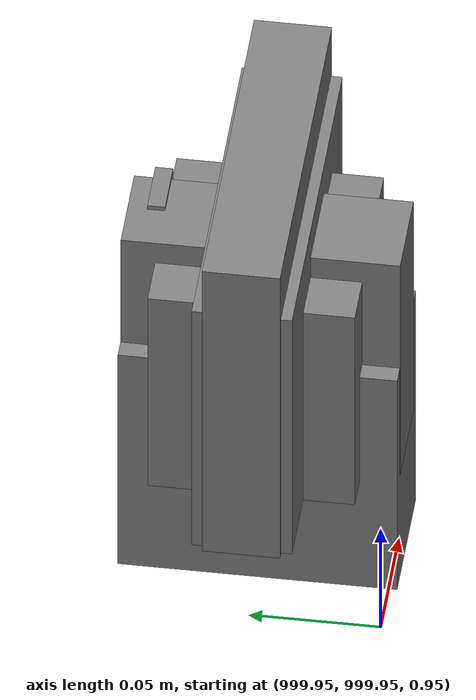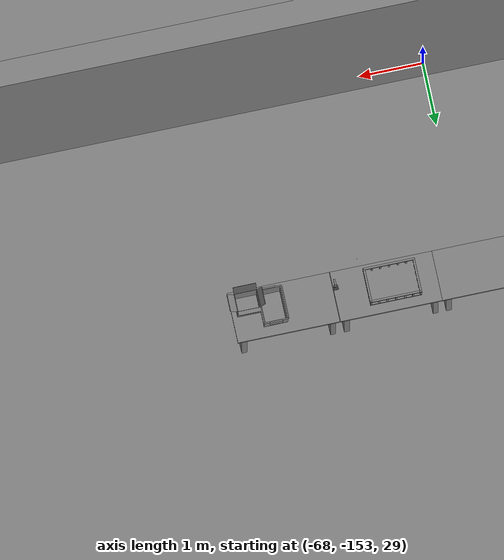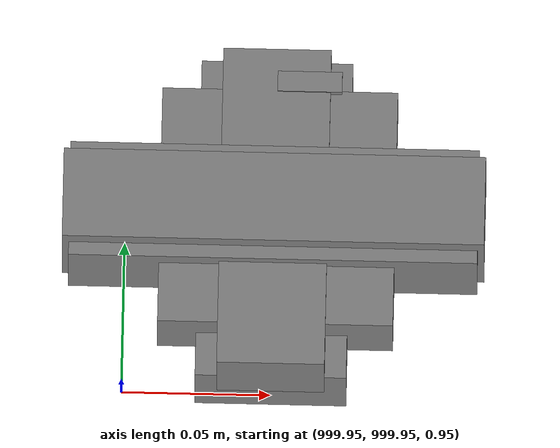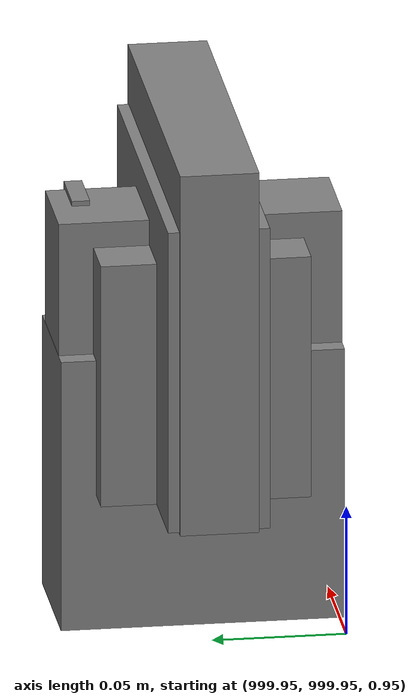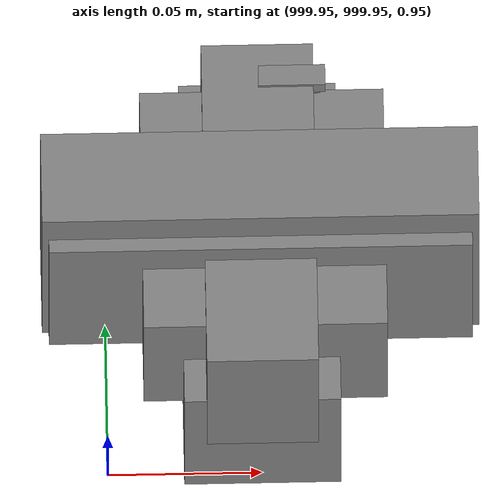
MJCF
<mujoco>
    <option gravity="0.000000000 0.000000000 -9.810000420" timestep="0.0049999999" integrator="implicitfast" density="1.225" viscosity="1.8000001e-05" noslip_iterations="10" iterations="100" sdf_iterations="50">
        <flag multiccd="disable"/>
    </option>
    <size memory="1000M"/>
    <compiler coordinate="local"/>
    <worldbody>
        <light cutoff="30" pos="0 1 1" dir="0 -1 -2"/>
        <light cutoff="30" pos="0 -1 1" dir="0 1 -2"/>
        <body pos="-64.866622925 -149.383972168 30.183746338" euler="89.999984741 89.999946594 0.000000000" name="openloong_gripper_2f85_fix_base_usda_bluebox_01">
            <geom contype="1" conaffinity="1" density="1000" type="box" material="" rgba="0.500000000 0.500000000 0.500000000 1.000000000" solimp="0.899999976 0.949999988 0.001000000" friction="1.000000000 0.005000000 0.000100000" solref="0.020000000 1.000000000" margin="0" condim="3" group="0" pos="0.276580811 0.187225342 0.000068665" quat="0.707106948 0.000077471 0.707106352 0.000077486" size="0.100000001 0.057999998 0.010000000" name="openloong_gripper_2f85_fix_base_usda_geom_5F1A7BC6_88FD_4470_B9CF_3BF443653CFB"/>
            <geom contype="1" conaffinity="1" density="1000" type="box" material="" rgba="0.500000000 0.500000000 0.500000000 1.000000000" solimp="0.899999976 0.949999988 0.001000000" friction="1.000000000 0.005000000 0.000100000" solref="0.020000000 1.000000000" margin="0" condim="3" group="0" pos="0.000000000 0.002883911 0.000000000" quat="0.999999881 0.000000000 0.000000000 0.000000000" size="0.254000008 0.003000000 0.172000006" name="openloong_gripper_2f85_fix_base_usda_geom_C3C2F274_B7EE_4200_87E3_1AA0FA3B3702"/>
            <geom contype="1" conaffinity="1" density="1000" type="box" material="" rgba="0.500000000 0.500000000 0.500000000 1.000000000" solimp="0.899999976 0.949999988 0.001000000" friction="1.000000000 0.005000000 0.000100000" solref="0.020000000 1.000000000" margin="0" condim="3" group="0" pos="0.000000000 0.124874115 0.173484802" quat="0.999796331 0.020176515 -0.000000015 0.000000030" size="0.259999990 0.119999997 0.007000000" name="openloong_gripper_2f85_fix_base_usda_geom_FDF222D8_A384_4DDC_B06D_8F68BFE49869"/>
            <geom contype="1" conaffinity="1" density="1000" type="box" material="" rgba="0.500000000 0.500000000 0.500000000 1.000000000" solimp="0.899999976 0.949999988 0.001000000" friction="1.000000000 0.005000000 0.000100000" solref="0.020000000 1.000000000" margin="0" condim="3" group="0" pos="0.000000000 0.124874115 -0.173469543" quat="0.999796331 -0.020176545 -0.000000015 0.000000000" size="0.259999990 0.119999997 0.007000000" name="openloong_gripper_2f85_fix_base_usda_geom_5FFF477F_BEE3_40B3_A14A_AF534907D768"/>
            <geom contype="1" conaffinity="1" density="1000" type="box" material="" rgba="0.500000000 0.500000000 0.500000000 1.000000000" solimp="0.899999976 0.949999988 0.001000000" friction="1.000000000 0.005000000 0.000100000" solref="0.020000000 1.000000000" margin="0" condim="3" group="0" pos="0.000000000 0.214008331 0.188980103" quat="0.999912977 0.013176724 0.000000015 0.000000000" size="0.259999990 0.029999999 0.012500000" name="openloong_gripper_2f85_fix_base_usda_geom_269FDA19_8339_49DA_B92F_50648964BE03"/>
            <geom contype="1" conaffinity="1" density="1000" type="box" material="" rgba="0.500000000 0.500000000 0.500000000 1.000000000" solimp="0.899999976 0.949999988 0.001000000" friction="1.000000000 0.005000000 0.000100000" solref="0.020000000 1.000000000" margin="0" condim="3" group="0" pos="-0.258361816 0.125289917 0.001876831" quat="0.702796936 -0.020792112 0.710783124 0.020769298" size="0.189999998 0.119999997 0.009000000" name="openloong_gripper_2f85_fix_base_usda_geom_13564649_9626_4BAE_A7F4_1E94F27925AE"/>
            <geom contype="1" conaffinity="1" density="1000" type="box" material="" rgba="0.500000000 0.500000000 0.500000000 1.000000000" solimp="0.899999976 0.949999988 0.001000000" friction="1.000000000 0.005000000 0.000100000" solref="0.020000000 1.000000000" margin="0" condim="3" group="0" pos="0.000000000 0.214008331 -0.188980103" quat="0.999912977 -0.013176769 0.000000030 0.000000015" size="0.259999990 0.029999999 0.012500000" name="openloong_gripper_2f85_fix_base_usda_geom_DA0BA7A9_E95E_4999_AF14_56A2E94E954D"/>
            <geom contype="1" conaffinity="1" density="1000" type="box" material="" rgba="0.500000000 0.500000000 0.500000000 1.000000000" solimp="0.899999976 0.949999988 0.001000000" friction="1.000000000 0.005000000 0.000100000" solref="0.020000000 1.000000000" margin="0" condim="3" group="0" pos="-0.276611328 0.187225342 0.000068665" quat="0.707106650 0.000077441 0.707106709 0.000077456" size="0.100000001 0.057999998 0.010000000" name="openloong_gripper_2f85_fix_base_usda_geom_F9776805_0FB4_4BE3_BBF0_CAA420610AEE"/>
            <geom contype="1" conaffinity="1" density="1000" type="box" material="" rgba="0.500000000 0.500000000 0.500000000 1.000000000" solimp="0.899999976 0.949999988 0.001000000" friction="1.000000000 0.005000000 0.000100000" solref="0.020000000 1.000000000" margin="0" condim="3" group="0" pos="0.258331299 0.125289917 0.001876831" quat="0.702851415 0.018856421 0.710823774 -0.019329369" size="0.189999998 0.119999997 0.009000000" name="openloong_gripper_2f85_fix_base_usda_geom_981EBC3B_2176_4CB8_AABD_FDDF90EA3810"/>
            <freejoint name="openloong_gripper_2f85_fix_base_usda_bluebox_01_joint"/>
            <site size="0.005000000 0.005000000 0.005000000" rgba="0.500000000 0.500000000 0.500000000 1.000000000" pos="0.000000000 0.000000000 0.000000000" quat="0.999961913 0.008726534 0.000000000 0.000000000" group="0" type="sphere" name="openloong_gripper_2f85_fix_base_usda_bluebox_01site"/>
        </body>
        <body pos="-64.496299744 -149.491867065 30.235729218" euler="0.000000000 0.000000000 89.999946594" name="openloong_gripper_2f85_fix_base_usda_cardboardbox_01">
            <geom contype="1" conaffinity="1" density="1000" type="box" material="" rgba="0.500000000 0.500000000 0.500000000 1.000000000" solimp="0.899999976 0.949999988 0.001000000" friction="1.000000000 0.005000000 0.000100000" solref="0.020000000 1.000000000" margin="0" condim="3" group="0" pos="-0.003166199 -0.004086494 0.005052090" quat="1.000000000 0.000000000 0.000000000 0.000000000" size="0.142499998 0.177500010 0.005000000" name="openloong_gripper_2f85_fix_base_usda_geom_691584D5_3BB2_4A4B_8222_9E78852FED1D"/>
            <geom contype="1" conaffinity="1" density="1000" type="box" material="" rgba="0.500000000 0.500000000 0.500000000 1.000000000" solimp="0.899999976 0.949999988 0.001000000" friction="1.000000000 0.005000000 0.000100000" solref="0.020000000 1.000000000" margin="0" condim="3" group="0" pos="-0.003166199 0.170316696 0.150570869" quat="1.000000000 0.000000000 0.000000000 0.000000000" size="0.142499998 0.005000000 0.149999991" name="openloong_gripper_2f85_fix_base_usda_geom_DAA33392_F204_4C20_8D56_DB379737A948"/>
            <geom contype="1" conaffinity="1" density="1000" type="box" material="" rgba="0.500000000 0.500000000 0.500000000 1.000000000" solimp="0.899999976 0.949999988 0.001000000" friction="1.000000000 0.005000000 0.000100000" solref="0.020000000 1.000000000" margin="0" condim="3" group="0" pos="-0.147399902 -0.005307198 0.150570869" quat="1.000000000 0.000000000 0.000000000 0.000000000" size="0.005000000 0.177500010 0.149999991" name="openloong_gripper_2f85_fix_base_usda_geom_E3A3EAB1_5D89_4B3B_8D98_E6DBC94E3FC8"/>
            <geom contype="1" conaffinity="1" density="1000" type="box" material="" rgba="0.500000000 0.500000000 0.500000000 1.000000000" solimp="0.899999976 0.949999988 0.001000000" friction="1.000000000 0.005000000 0.000100000" solref="0.020000000 1.000000000" margin="0" condim="3" group="0" pos="0.140275955 -0.005307198 0.150570869" quat="1.000000000 0.000000000 0.000000000 0.000000000" size="0.005000000 0.177500010 0.149999991" name="openloong_gripper_2f85_fix_base_usda_geom_0C04EE85_73EB_44BF_8BEE_6F7BDB56AA98"/>
            <geom contype="1" conaffinity="1" density="1000" type="box" material="" rgba="0.500000000 0.500000000 0.500000000 1.000000000" solimp="0.899999976 0.949999988 0.001000000" friction="1.000000000 0.005000000 0.000100000" solref="0.020000000 1.000000000" margin="0" condim="3" group="0" pos="-0.003166199 -0.181550980 0.150570869" quat="1.000000000 0.000000000 0.000000000 0.000000000" size="0.142499998 0.005000000 0.149999991" name="openloong_gripper_2f85_fix_base_usda_geom_54E097EF_CE7D_444A_8F5B_D3B55475F75C"/>
            <freejoint name="openloong_gripper_2f85_fix_base_usda_cardboardbox_01_joint"/>
            <site size="0.005000000 0.005000000 0.005000000" rgba="0.500000000 0.500000000 0.500000000 1.000000000" pos="0.000000000 0.000000000 0.000000000" quat="0.999961913 0.008726535 0.000000000 0.000000000" group="0" type="sphere" name="openloong_gripper_2f85_fix_base_usda_site_D70A797C_5D4B_437A_A7D1_5B7676D60831"/>
            <body pos="0.139160156 -0.004048347 0.301930904" euler="-179.999954224 49.383502960 179.999954224" name="openloong_gripper_2f85_fix_base_usda_A1_006">
                <geom contype="1" conaffinity="1" density="1000" type="box" material="" rgba="0.500000000 0.500000000 0.500000000 1.000000000" solimp="0.899999976 0.949999988 0.001000000" friction="1.000000000 0.005000000 0.000100000" solref="0.020000000 1.000000000" margin="0" condim="3" group="0" pos="-0.071587563 0.000009537 0.001745224" quat="0.999999881 0.000000000 0.000000000 0.000000000" size="0.071249999 0.179999992 0.002500000" name="openloong_gripper_2f85_fix_base_usda_geom_28D869C0_DF2F_4502_92F9_A284F0901E41"/>
                <joint armature="0" stiffness="0.07" damping="0.0099999998" axis="0.000000 1.000000 0.000000" type="hinge" name="openloong_gripper_2f85_fix_base_usda_A1_006"/>
            </body>
            <body pos="-0.145902634 -0.004086494 0.301938057" euler="-180.000000000 -60.000011444 -180.000000000" name="openloong_gripper_2f85_fix_base_usda_A2_006">
                <geom contype="1" conaffinity="1" density="1000" type="box" material="" rgba="0.500000000 0.500000000 0.500000000 1.000000000" solimp="0.899999976 0.949999988 0.001000000" friction="1.000000000 0.005000000 0.000100000" solref="0.020000000 1.000000000" margin="0" condim="3" group="0" pos="0.071268082 0.000009537 0.002717972" quat="0.000002921 0.000000000 -0.000000030 0.999999881" size="0.071249999 0.179999992 0.002500000" name="openloong_gripper_2f85_fix_base_usda_geom_EE3F6B52_01A3_4A0E_B906_CA16931F62EB"/>
                <joint armature="0" stiffness="0.07" damping="0.0099999998" axis="0.000000 1.000000 0.000000" type="hinge" name="openloong_gripper_2f85_fix_base_usda_A2_006"/>
            </body>
            <body pos="-0.003385544 0.175991058 0.301930904" euler="-125.858116150 -0.000004561 0.000002331" name="openloong_gripper_2f85_fix_base_usda_B2_006">
                <geom contype="1" conaffinity="1" density="1000" type="box" material="" rgba="0.500000000 0.500000000 0.500000000 1.000000000" solimp="0.899999976 0.949999988 0.001000000" friction="1.000000000 0.005000000 0.000100000" solref="0.020000000 1.000000000" margin="0" condim="3" group="0" pos="0.000009537 -0.070939064 -0.002470016" quat="0.999614120 0.027776197 -0.000000015 0.000000030" size="0.137500003 0.064999998 0.005000000" name="openloong_gripper_2f85_fix_base_usda_geom_494B32F9_EE0C_490B_A74E_ED168489DC65"/>
                <joint armature="0" stiffness="0.07" damping="0.0099999998" axis="1.000000 0.000000 0.000000" type="hinge" name="openloong_gripper_2f85_fix_base_usda_B2_006"/>
            </body>
            <body pos="-0.003385544 -0.184140205 0.301938057" euler="147.805557251 0.000000000 0.000000000" name="openloong_gripper_2f85_fix_base_usda_B1_006">
                <geom contype="1" conaffinity="1" density="1000" type="box" material="" rgba="0.500000000 0.500000000 0.500000000 1.000000000" solimp="0.899999976 0.949999988 0.001000000" friction="1.000000000 0.005000000 0.000100000" solref="0.020000000 1.000000000" margin="0" condim="3" group="0" pos="-0.000028610 0.070202351 -0.002703667" quat="0.999614179 -0.027776167 0.000000000 0.000000000" size="0.137500003 0.064999998 0.005000000" name="openloong_gripper_2f85_fix_base_usda_geom_83EEEEC0_0C67_49CB_89E4_7CF22704DB88"/>
                <joint armature="0" stiffness="0.07" damping="0.0099999998" axis="1.000000 0.000000 0.000000" type="hinge" name="openloong_gripper_2f85_fix_base_usda_B1_006"/>
            </body>
        </body>
        <body pos="-65.882858276 -149.481979370 30.229999542" euler="-64.487716675 0.000000000 0.000000000" name="openloong_gripper_2f85_fix_base_usda_Barcode">
            <geom contype="1" conaffinity="1" density="1000" type="box" material="" rgba="0.500000000 0.500000000 0.500000000 1.000000000" solimp="0.899999976 0.949999988 0.001000000" friction="1.000000000 0.005000000 0.000100000" solref="0.020000000 1.000000000" margin="0" condim="3" group="0" pos="0.000000000 0.013038635 0.001419067" quat="0.000000000 0.000000000 0.000000000 1.000000119" size="0.034000002 0.010000000 0.017999999" name="openloong_gripper_2f85_fix_base_usda_geom_64E20CFE_B908_48C3_BC24_52C084B3A053"/>
            <geom contype="1" conaffinity="1" density="1000" type="box" material="" rgba="0.500000000 0.500000000 0.500000000 1.000000000" solimp="0.899999976 0.949999988 0.001000000" friction="1.000000000 0.005000000 0.000100000" solref="0.020000000 1.000000000" margin="0" condim="3" group="0" pos="0.000000000 -0.035301208 -0.007095337" quat="0.000000000 0.000000000 -0.043619365 0.999048233" size="0.028999999 0.010000000 0.020000000" name="openloong_gripper_2f85_fix_base_usda_geom_AF3B7B60_1CAC_4B4B_8698_694375FA0E89"/>
            <geom contype="1" conaffinity="1" density="1000" type="box" material="" rgba="0.500000000 0.500000000 0.500000000 1.000000000" solimp="0.899999976 0.949999988 0.001000000" friction="1.000000000 0.005000000 0.000100000" solref="0.020000000 1.000000000" margin="0" condim="3" group="0" pos="0.000000000 -0.043411255 -0.011749268" quat="0.922262907 0.386563420 0.000000000 0.000000000" size="0.026000001 0.010000000 0.020000000" name="openloong_gripper_2f85_fix_base_usda_geom_81981D78_B890_4DD1_8939_8AA75A488301"/>
            <geom contype="1" conaffinity="1" density="1000" type="box" material="" rgba="0.500000000 0.500000000 0.500000000 1.000000000" solimp="0.899999976 0.949999988 0.001000000" friction="1.000000000 0.005000000 0.000100000" solref="0.020000000 1.000000000" margin="0" condim="3" group="0" pos="0.000000000 -0.016967773 -0.031860352" quat="0.000000000 0.000000000 0.000000000 1.000000119" size="0.008000000 0.010000000 0.013000000" name="openloong_gripper_2f85_fix_base_usda_geom_254C019D_D675_4735_8CD8_6D2CB2B721DC"/>
            <geom contype="1" conaffinity="1" density="1000" type="box" material="" rgba="0.500000000 0.500000000 0.500000000 1.000000000" solimp="0.899999976 0.949999988 0.001000000" friction="1.000000000 0.005000000 0.000100000" solref="0.020000000 1.000000000" margin="0" condim="3" group="0" pos="0.000000000 -0.001869202 0.000312805" quat="0.953716993 0.300705761 0.000000000 0.000000000" size="0.032000002 0.010000000 0.018999999" name="openloong_gripper_2f85_fix_base_usda_geom_90B42FE0_6FEE_45CF_9173_1BF5A981B2E0"/>
            <geom contype="1" conaffinity="1" density="1000" type="box" material="" rgba="0.500000000 0.500000000 0.500000000 1.000000000" solimp="0.899999976 0.949999988 0.001000000" friction="1.000000000 0.005000000 0.000100000" solref="0.020000000 1.000000000" margin="0" condim="3" group="0" pos="0.000000000 -0.019531250 -0.003173828" quat="0.953716993 0.300705761 0.000000000 0.000000000" size="0.030999999 0.010000000 0.020000000" name="openloong_gripper_2f85_fix_base_usda_geom_94C8BDF7_F444_44A9_999F_D8545588ABDA"/>
            <geom contype="1" conaffinity="1" density="1000" type="box" material="" rgba="0.500000000 0.500000000 0.500000000 1.000000000" solimp="0.899999976 0.949999988 0.001000000" friction="1.000000000 0.005000000 0.000100000" solref="0.020000000 1.000000000" margin="0" condim="3" group="0" pos="0.000000000 -0.035301208 -0.007095337" quat="0.953716993 0.300705761 0.000000000 0.000000000" size="0.028999999 0.010000000 0.020000000" name="openloong_gripper_2f85_fix_base_usda_geom_374F4322_30BA_4DAF_A145_B2A5FCB8794B"/>
            <geom contype="1" conaffinity="1" density="1000" type="box" material="" rgba="0.500000000 0.500000000 0.500000000 1.000000000" solimp="0.899999976 0.949999988 0.001000000" friction="1.000000000 0.005000000 0.000100000" solref="0.020000000 1.000000000" margin="0" condim="3" group="0" pos="0.000000000 -0.042617798 -0.071121216" quat="0.000000000 0.000000000 0.000000000 1.000000119" size="0.013000000 0.021000000 0.059999999" name="openloong_gripper_2f85_fix_base_usda_geom_38B0FD85_0AEF_494E_B9EC_4AE30984C364"/>
            <freejoint name="openloong_gripper_2f85_fix_base_usda_Barcode_joint"/>
            <site size="0.005000000 0.005000000 0.005000000" rgba="0.500000000 0.500000000 0.500000000 1.000000000" pos="0.000000000 0.000000000 0.000000000" quat="1.000000000 0.000000000 0.000000000 0.000000000" group="0" type="sphere" name="openloong_gripper_2f85_fix_base_usda_Barcode_site"/>
        </body>
        <body pos="-66.745018005 -149.392349243 30.184000015" euler="0.000000000 0.000000000 89.999946594" name="[22333127228603]_Basket_01">
            <geom contype="1" conaffinity="1" density="1000" type="box" material="" rgba="0.500000000 0.500000000 0.500000000 1.000000000" solimp="0.899999976 0.949999988 0.001000000" friction="1.000000000 0.005000000 0.000100000" solref="0.020000000 1.000000000" margin="0" condim="3" group="0" pos="-0.052425385 0.389207840 0.089787483" quat="0.707107008 0.000000000 0.000000000 0.707106411" size="0.014249999 0.014249999 0.059999999" name="[22333127228603]_geom_F9033C0E_7FB2_48DA_BD91_61403A8D9B3B"/>
            <geom contype="1" conaffinity="1" density="1000" type="box" material="" rgba="0.500000000 0.500000000 0.500000000 1.000000000" solimp="0.899999976 0.949999988 0.001000000" friction="1.000000000 0.005000000 0.000100000" solref="0.020000000 1.000000000" margin="0" condim="3" group="0" pos="0.264015198 -0.133043289 0.089787483" quat="0.707107008 0.000000000 0.000000000 0.707106411" size="0.014249999 0.014249999 0.059999999" name="[22333127228603]_geom_6B5B8753_98CB_42AC_976B_8B7485FD0BC3"/>
            <geom contype="1" conaffinity="1" density="1000" type="box" material="" rgba="0.500000000 0.500000000 0.500000000 1.000000000" solimp="0.899999976 0.949999988 0.001000000" friction="1.000000000 0.005000000 0.000100000" solref="0.020000000 1.000000000" margin="0" condim="3" group="0" pos="-0.264015198 -0.265548706 0.089793205" quat="0.707107008 0.000000000 0.000000000 0.707106411" size="0.014249999 0.014249999 0.059999999" name="[22333127228603]_geom_9ED8FFEE_CA5E_44D3_80C5_AE70DCEE7482"/>
            <geom contype="1" conaffinity="1" density="1000" type="box" material="" rgba="0.500000000 0.500000000 0.500000000 1.000000000" solimp="0.899999976 0.949999988 0.001000000" friction="1.000000000 0.005000000 0.000100000" solref="0.020000000 1.000000000" margin="0" condim="3" group="0" pos="-0.160263062 -0.389322281 0.089793205" quat="0.707107008 0.000000000 0.000000000 0.707106411" size="0.014249999 0.014249999 0.059999999" name="[22333127228603]_geom_23D777D1_3547_4C2F_A657_B08C4944F8E4"/>
            <geom contype="1" conaffinity="1" density="1000" type="box" material="" rgba="0.500000000 0.500000000 0.500000000 1.000000000" solimp="0.899999976 0.949999988 0.001000000" friction="1.000000000 0.005000000 0.000100000" solref="0.020000000 1.000000000" margin="0" condim="3" group="0" pos="0.162265778 -0.389322281 0.089787483" quat="0.707107008 0.000000000 0.000000000 0.707106411" size="0.014249999 0.014249999 0.059999999" name="[22333127228603]_geom_2A30CE59_29A7_467C_AE92_E7ABD8EA26D8"/>
            <geom contype="1" conaffinity="1" density="1000" type="box" material="" rgba="0.500000000 0.500000000 0.500000000 1.000000000" solimp="0.899999976 0.949999988 0.001000000" friction="1.000000000 0.005000000 0.000100000" solref="0.020000000 1.000000000" margin="0" condim="3" group="0" pos="0.264015198 0.389207840 0.089787483" quat="0.707107008 0.000000000 0.000000000 0.707106411" size="0.014249999 0.014249999 0.059999999" name="[22333127228603]_geom_C6C01905_E699_44F2_A63D_C61B10264B22"/>
            <geom contype="1" conaffinity="1" density="1000" type="box" material="" rgba="0.500000000 0.500000000 0.500000000 1.000000000" solimp="0.899999976 0.949999988 0.001000000" friction="1.000000000 0.005000000 0.000100000" solref="0.020000000 1.000000000" margin="0" condim="3" group="0" pos="-0.264015198 -0.133043289 0.089793205" quat="0.707107008 0.000000000 0.000000000 0.707106411" size="0.014249999 0.014249999 0.059999999" name="[22333127228603]_geom_B380148B_9644_458B_B990_B015CB4693B8"/>
            <geom contype="1" conaffinity="1" density="1000" type="box" material="" rgba="0.500000000 0.500000000 0.500000000 1.000000000" solimp="0.899999976 0.949999988 0.001000000" friction="1.000000000 0.005000000 0.000100000" solref="0.020000000 1.000000000" margin="0" condim="3" group="0" pos="-0.264026642 0.269256592 0.089793205" quat="0.707107008 0.000000000 0.000000000 0.707106411" size="0.014249999 0.014249999 0.059999999" name="[22333127228603]_geom_E8CBA257_BAFD_401B_B4FF_4E2B1CD1B224"/>
            <geom contype="1" conaffinity="1" density="1000" type="box" material="" rgba="0.500000000 0.500000000 0.500000000 1.000000000" solimp="0.899999976 0.949999988 0.001000000" friction="1.000000000 0.005000000 0.000100000" solref="0.020000000 1.000000000" margin="0" condim="3" group="0" pos="0.054462433 0.389207840 0.089787483" quat="0.707107008 0.000000000 0.000000000 0.707106411" size="0.014249999 0.014249999 0.059999999" name="[22333127228603]_geom_2B65CF6E_C440_47C2_A900_D26DDA792A21"/>
            <geom contype="1" conaffinity="1" density="1000" type="box" material="" rgba="0.500000000 0.500000000 0.500000000 1.000000000" solimp="0.899999976 0.949999988 0.001000000" friction="1.000000000 0.005000000 0.000100000" solref="0.020000000 1.000000000" margin="0" condim="3" group="0" pos="0.054462433 -0.389322281 0.089787483" quat="0.707107008 0.000000000 0.000000000 0.707106411" size="0.014249999 0.014249999 0.059999999" name="[22333127228603]_geom_62FF5B34_2372_4366_AB80_9AC2635A29BA"/>
            <geom contype="1" conaffinity="1" density="1000" type="box" material="" rgba="0.500000000 0.500000000 0.500000000 1.000000000" solimp="0.899999976 0.949999988 0.001000000" friction="1.000000000 0.005000000 0.000100000" solref="0.020000000 1.000000000" margin="0" condim="3" group="0" pos="0.264015198 0.269256592 0.089793205" quat="0.707107008 0.000000000 0.000000000 0.707106411" size="0.014249999 0.014249999 0.059999999" name="[22333127228603]_geom_682E85B5_E503_4804_A51C_85E3A656DAD0"/>
            <geom contype="1" conaffinity="1" density="1000" type="box" material="" rgba="0.500000000 0.500000000 0.500000000 1.000000000" solimp="0.899999976 0.949999988 0.001000000" friction="1.000000000 0.005000000 0.000100000" solref="0.020000000 1.000000000" margin="0" condim="3" group="0" pos="0.264015198 -0.389322281 0.089787483" quat="0.707107008 0.000000000 0.000000000 0.707106411" size="0.014249999 0.014249999 0.059999999" name="[22333127228603]_geom_5114A9BF_74C2_4126_AFA1_58F2E4514FBD"/>
            <geom contype="1" conaffinity="1" density="1000" type="box" material="" rgba="0.500000000 0.500000000 0.500000000 1.000000000" solimp="0.899999976 0.949999988 0.001000000" friction="1.000000000 0.005000000 0.000100000" solref="0.020000000 1.000000000" margin="0" condim="3" group="0" pos="0.000000000 0.000000000 0.015998840" quat="0.707107008 0.000000000 0.000000000 0.707106411" size="0.403499991 0.279000014 0.015750000" name="[22333127228603]_geom_C1432E85_60B9_458E_A604_B2B76396B88B"/>
            <geom contype="1" conaffinity="1" density="1000" type="box" material="" rgba="0.500000000 0.500000000 0.500000000 1.000000000" solimp="0.899999976 0.949999988 0.001000000" friction="1.000000000 0.005000000 0.000100000" solref="0.020000000 1.000000000" margin="0" condim="3" group="0" pos="0.000000000 -0.389476776 0.163619041" quat="0.707107008 0.000000000 0.000000000 0.707106411" size="0.015000000 0.277500004 0.015750000" name="[22333127228603]_geom_F2DAC6B8_81D0_4034_ABBA_99DD8C8F76B6"/>
            <geom contype="1" conaffinity="1" density="1000" type="box" material="" rgba="0.500000000 0.500000000 0.500000000 1.000000000" solimp="0.899999976 0.949999988 0.001000000" friction="1.000000000 0.005000000 0.000100000" solref="0.020000000 1.000000000" margin="0" condim="3" group="0" pos="0.162265778 0.389207840 0.089787483" quat="0.707107008 0.000000000 0.000000000 0.707106411" size="0.014249999 0.014249999 0.059999999" name="[22333127228603]_geom_CEFE2395_93EF_4AC3_AF1E_F46F48041239"/>
            <geom contype="1" conaffinity="1" density="1000" type="box" material="" rgba="0.500000000 0.500000000 0.500000000 1.000000000" solimp="0.899999976 0.949999988 0.001000000" friction="1.000000000 0.005000000 0.000100000" solref="0.020000000 1.000000000" margin="0" condim="3" group="0" pos="0.000000000 0.389471054 0.163619041" quat="0.707107008 0.000000000 0.000000000 0.707106411" size="0.015000000 0.277500004 0.015750000" name="[22333127228603]_geom_51C41F0C_65AE_453B_91E1_5AB9C20F4CA3"/>
            <geom contype="1" conaffinity="1" density="1000" type="box" material="" rgba="0.500000000 0.500000000 0.500000000 1.000000000" solimp="0.899999976 0.949999988 0.001000000" friction="1.000000000 0.005000000 0.000100000" solref="0.020000000 1.000000000" margin="0" condim="3" group="0" pos="-0.263511658 0.000000000 0.163619041" quat="0.707107008 0.000000000 0.000000000 0.707106411" size="0.403499991 0.015000000 0.015750000" name="[22333127228603]_geom_62B459A5_4505_4C19_8DF1_76D05E0B7958"/>
            <geom contype="1" conaffinity="1" density="1000" type="box" material="" rgba="0.500000000 0.500000000 0.500000000 1.000000000" solimp="0.899999976 0.949999988 0.001000000" friction="1.000000000 0.005000000 0.000100000" solref="0.020000000 1.000000000" margin="0" condim="3" group="0" pos="-0.264015198 0.141334534 0.089793205" quat="0.707107008 0.000000000 0.000000000 0.707106411" size="0.014249999 0.014249999 0.059999999" name="[22333127228603]_geom_1DEA53D3_AEA2_49D2_9E3A_FF792660E4B8"/>
            <geom contype="1" conaffinity="1" density="1000" type="box" material="" rgba="0.500000000 0.500000000 0.500000000 1.000000000" solimp="0.899999976 0.949999988 0.001000000" friction="1.000000000 0.005000000 0.000100000" solref="0.020000000 1.000000000" margin="0" condim="3" group="0" pos="0.264015198 -0.265548706 0.089787483" quat="0.707107008 0.000000000 0.000000000 0.707106411" size="0.014249999 0.014249999 0.059999999" name="[22333127228603]_geom_BA4A3B48_47FC_4A59_883C_AF35AB0E1C31"/>
            <geom contype="1" conaffinity="1" density="1000" type="box" material="" rgba="0.500000000 0.500000000 0.500000000 1.000000000" solimp="0.899999976 0.949999988 0.001000000" friction="1.000000000 0.005000000 0.000100000" solref="0.020000000 1.000000000" margin="0" condim="3" group="0" pos="-0.160263062 0.389207840 0.089787483" quat="0.707107008 0.000000000 0.000000000 0.707106411" size="0.014249999 0.014249999 0.059999999" name="[22333127228603]_geom_CB4D733E_EEFB_49E1_9ABC_24D0A7E8258F"/>
            <geom contype="1" conaffinity="1" density="1000" type="box" material="" rgba="0.500000000 0.500000000 0.500000000 1.000000000" solimp="0.899999976 0.949999988 0.001000000" friction="1.000000000 0.005000000 0.000100000" solref="0.020000000 1.000000000" margin="0" condim="3" group="0" pos="-0.052425385 -0.389322281 0.089787483" quat="0.707107008 0.000000000 0.000000000 0.707106411" size="0.014249999 0.014249999 0.059999999" name="[22333127228603]_geom_96C11CD0_9B27_4C8D_9E1D_A1546F498369"/>
            <geom contype="1" conaffinity="1" density="1000" type="box" material="" rgba="0.500000000 0.500000000 0.500000000 1.000000000" solimp="0.899999976 0.949999988 0.001000000" friction="1.000000000 0.005000000 0.000100000" solref="0.020000000 1.000000000" margin="0" condim="3" group="0" pos="-0.264026642 -0.389322281 0.089793205" quat="0.707107008 0.000000000 0.000000000 0.707106411" size="0.014249999 0.014249999 0.059999999" name="[22333127228603]_geom_14EB7B66_5F82_4674_93FA_AAD3241D1AB8"/>
            <geom contype="1" conaffinity="1" density="1000" type="box" material="" rgba="0.500000000 0.500000000 0.500000000 1.000000000" solimp="0.899999976 0.949999988 0.001000000" friction="1.000000000 0.005000000 0.000100000" solref="0.020000000 1.000000000" margin="0" condim="3" group="0" pos="0.264015198 0.141334534 0.089787483" quat="0.707107008 0.000000000 0.000000000 0.707106411" size="0.014249999 0.014249999 0.059999999" name="[22333127228603]_geom_F975CEF8_2375_440C_BB44_126340B21857"/>
            <geom contype="1" conaffinity="1" density="1000" type="box" material="" rgba="0.500000000 0.500000000 0.500000000 1.000000000" solimp="0.899999976 0.949999988 0.001000000" friction="1.000000000 0.005000000 0.000100000" solref="0.020000000 1.000000000" margin="0" condim="3" group="0" pos="-0.264015198 0.389207840 0.089793205" quat="0.707107008 0.000000000 0.000000000 0.707106411" size="0.014249999 0.014249999 0.059999999" name="[22333127228603]_geom_64B1B528_160C_4822_B55F_05CAECB79089"/>
            <geom contype="1" conaffinity="1" density="1000" type="box" material="" rgba="0.500000000 0.500000000 0.500000000 1.000000000" solimp="0.899999976 0.949999988 0.001000000" friction="1.000000000 0.005000000 0.000100000" solref="0.020000000 1.000000000" margin="0" condim="3" group="0" pos="0.264015198 0.004480362 0.089787483" quat="0.707107008 0.000000000 0.000000000 0.707106411" size="0.014249999 0.014249999 0.059999999" name="[22333127228603]_geom_415D3F05_981E_43D1_A449_0BD1D4B7B6FB"/>
            <geom contype="1" conaffinity="1" density="1000" type="box" material="" rgba="0.500000000 0.500000000 0.500000000 1.000000000" solimp="0.899999976 0.949999988 0.001000000" friction="1.000000000 0.005000000 0.000100000" solref="0.020000000 1.000000000" margin="0" condim="3" group="0" pos="0.263694763 -0.000011444 0.163619041" quat="0.707107008 0.000000000 0.000000000 0.707106411" size="0.403499991 0.015000000 0.015750000" name="[22333127228603]_geom_8ECCD856_DF9C_4313_8F12_B4162CFF6643"/>
            <geom contype="1" conaffinity="1" density="1000" type="box" material="" rgba="0.500000000 0.500000000 0.500000000 1.000000000" solimp="0.899999976 0.949999988 0.001000000" friction="1.000000000 0.005000000 0.000100000" solref="0.020000000 1.000000000" margin="0" condim="3" group="0" pos="-0.264015198 0.004480362 0.089793205" quat="0.707107008 0.000000000 0.000000000 0.707106411" size="0.014249999 0.014249999 0.059999999" name="[22333127228603]_geom_2ED0D32D_8CF3_495E_BEF5_E827B724ACF7"/>
            <freejoint name="[22333127228603]_joint_75866F52_3804_41AC_9973_0F4CCB307082"/>
        </body>
        <body pos="0.000000000 0.000000000 0.000000000" euler="0.000000000 0.000000000 0.000000000" name="Static Objects_Static Objects">
            <geom contype="1" conaffinity="1" density="1000" type="box" material="" rgba="0.500000000 0.500000000 0.500000000 1.000000000" solimp="0.899999976 0.949999988 0.001000000" friction="1.000000000 0.005000000 0.000100000" solref="0.020000000 1.000000000" margin="0" condim="3" group="0" pos="-67.544113159 -149.365814209 29.727830887" quat="0.500000417 0.499999970 0.499999553 0.499999970" size="0.381000012 0.319999993 0.041000001" name="Static Objects_geom_9119D353_7976_487F_A9D0_48F6E9140C01"/>
            <geom contype="1" conaffinity="1" density="1000" type="box" material="" rgba="0.500000000 0.500000000 0.500000000 1.000000000" solimp="0.899999976 0.949999988 0.001000000" friction="1.000000000 0.005000000 0.000100000" solref="0.020000000 1.000000000" margin="0" condim="3" group="0" pos="-68.239501953 -149.365814209 30.086868286" quat="0.500000417 0.499999970 0.499999553 0.499999970" size="0.370999992 0.039500002 0.745000005" name="Static Objects_geom_3EFD7941_E3FD_4A5F_A44E_B916E1C198FA"/>
            <geom contype="1" conaffinity="1" density="1000" type="box" material="" rgba="0.500000000 0.500000000 0.500000000 1.000000000" solimp="0.899999976 0.949999988 0.001000000" friction="1.000000000 0.005000000 0.000100000" solref="0.020000000 1.000000000" margin="0" condim="3" group="0" pos="-68.239501953 -149.365814209 30.147235870" quat="0.500000417 0.499999970 0.499999553 0.499999970" size="0.400000006 0.022000000 0.800000012" name="Static Objects_geom_769FB45B_4553_462D_A1EC_2532FA927704"/>
            <geom contype="1" conaffinity="1" density="1000" type="box" material="" rgba="0.500000000 0.500000000 0.500000000 1.000000000" solimp="0.899999976 0.949999988 0.001000000" friction="1.000000000 0.005000000 0.000100000" solref="0.020000000 1.000000000" margin="0" condim="3" group="0" pos="-68.934890747 -149.365814209 29.727830887" quat="0.500000417 0.499999970 0.499999553 0.499999970" size="0.381000012 0.319999993 0.041000001" name="Static Objects_geom_8CE2D3BF_CB16_43F7_842A_99F6F3E678BB"/>
            <geom contype="1" conaffinity="1" density="1000" type="box" material="" rgba="0.500000000 0.500000000 0.500000000 1.000000000" solimp="0.899999976 0.949999988 0.001000000" friction="1.000000000 0.005000000 0.000100000" solref="0.020000000 1.000000000" margin="0" condim="3" group="0" pos="-68.239501953 -149.365814209 29.561563492" quat="0.500000417 0.499999970 0.499999553 0.499999970" size="0.020000000 0.022000000 0.660000026" name="Static Objects_geom_ED3601A1_E818_487F_8FC6_457A90896DD5"/>
            <geom contype="1" conaffinity="1" density="1000" type="box" material="" rgba="0.500000000 0.500000000 0.500000000 1.000000000" solimp="0.899999976 0.949999988 0.001000000" friction="1.000000000 0.005000000 0.000100000" solref="0.020000000 1.000000000" margin="0" condim="3" group="0" pos="-65.945671082 -149.365814209 29.727830887" quat="0.500000417 0.499999970 0.499999553 0.499999970" size="0.381000012 0.319999993 0.041000001" name="Static Objects_geom_B63F2633_C321_45E6_9550_770F39F141E6"/>
            <geom contype="1" conaffinity="1" density="1000" type="box" material="" rgba="0.500000000 0.500000000 0.500000000 1.000000000" solimp="0.899999976 0.949999988 0.001000000" friction="1.000000000 0.005000000 0.000100000" solref="0.020000000 1.000000000" margin="0" condim="3" group="0" pos="-66.641059875 -149.365814209 30.086868286" quat="0.500000417 0.499999970 0.499999553 0.499999970" size="0.370999992 0.039500002 0.745000005" name="Static Objects_geom_90A7C846_243D_482B_8324_CA57D18F0D80"/>
            <geom contype="1" conaffinity="1" density="1000" type="box" material="" rgba="0.500000000 0.500000000 0.500000000 1.000000000" solimp="0.899999976 0.949999988 0.001000000" friction="1.000000000 0.005000000 0.000100000" solref="0.020000000 1.000000000" margin="0" condim="3" group="0" pos="-66.641059875 -149.365814209 30.147235870" quat="0.500000417 0.499999970 0.499999553 0.499999970" size="0.400000006 0.022000000 0.800000012" name="Static Objects_geom_5B99CBAF_9D2E_464A_9162_71551944EA32"/>
            <geom contype="1" conaffinity="1" density="1000" type="box" material="" rgba="0.500000000 0.500000000 0.500000000 1.000000000" solimp="0.899999976 0.949999988 0.001000000" friction="1.000000000 0.005000000 0.000100000" solref="0.020000000 1.000000000" margin="0" condim="3" group="0" pos="-67.336448669 -149.365814209 29.727830887" quat="0.500000417 0.499999970 0.499999553 0.499999970" size="0.381000012 0.319999993 0.041000001" name="Static Objects_geom_C770B1E0_CEF5_440E_88D8_A80F5D2D2D45"/>
            <geom contype="1" conaffinity="1" density="1000" type="box" material="" rgba="0.500000000 0.500000000 0.500000000 1.000000000" solimp="0.899999976 0.949999988 0.001000000" friction="1.000000000 0.005000000 0.000100000" solref="0.020000000 1.000000000" margin="0" condim="3" group="0" pos="-66.641059875 -149.365814209 29.561563492" quat="0.500000417 0.499999970 0.499999553 0.499999970" size="0.020000000 0.022000000 0.660000026" name="Static Objects_geom_97FE712D_9D3C_4194_8329_8C7B946B18EA"/>
            <geom contype="1" conaffinity="1" density="1000" type="box" material="" rgba="0.500000000 0.500000000 0.500000000 1.000000000" solimp="0.899999976 0.949999988 0.001000000" friction="1.000000000 0.005000000 0.000100000" solref="0.020000000 1.000000000" margin="0" condim="3" group="0" pos="-64.338577271 -149.365814209 29.727830887" quat="0.500000417 0.499999970 0.499999553 0.499999970" size="0.381000012 0.319999993 0.041000001" name="Static Objects_geom_28EA4A00_FD25_432E_B81A_53D172F1AADE"/>
            <geom contype="1" conaffinity="1" density="1000" type="box" material="" rgba="0.500000000 0.500000000 0.500000000 1.000000000" solimp="0.899999976 0.949999988 0.001000000" friction="1.000000000 0.005000000 0.000100000" solref="0.020000000 1.000000000" margin="0" condim="3" group="0" pos="-65.033966064 -149.365814209 30.086868286" quat="0.500000417 0.499999970 0.499999553 0.499999970" size="0.370999992 0.039500002 0.745000005" name="Static Objects_geom_B545ABC1_5171_4B2A_AE2A_E4ACDB14513D"/>
            <geom contype="1" conaffinity="1" density="1000" type="box" material="" rgba="0.500000000 0.500000000 0.500000000 1.000000000" solimp="0.899999976 0.949999988 0.001000000" friction="1.000000000 0.005000000 0.000100000" solref="0.020000000 1.000000000" margin="0" condim="3" group="0" pos="-65.033966064 -149.365814209 30.147235870" quat="0.500000417 0.499999970 0.499999553 0.499999970" size="0.400000006 0.022000000 0.800000012" name="Static Objects_geom_249A870D_2C64_4CFD_A334_47C87C6759DA"/>
            <geom contype="1" conaffinity="1" density="1000" type="box" material="" rgba="0.500000000 0.500000000 0.500000000 1.000000000" solimp="0.899999976 0.949999988 0.001000000" friction="1.000000000 0.005000000 0.000100000" solref="0.020000000 1.000000000" margin="0" condim="3" group="0" pos="-65.729354858 -149.365814209 29.727830887" quat="0.500000417 0.499999970 0.499999553 0.499999970" size="0.381000012 0.319999993 0.041000001" name="Static Objects_geom_407EDBEE_4A91_4748_8982_2EAD006D441E"/>
            <geom contype="1" conaffinity="1" density="1000" type="box" material="" rgba="0.500000000 0.500000000 0.500000000 1.000000000" solimp="0.899999976 0.949999988 0.001000000" friction="1.000000000 0.005000000 0.000100000" solref="0.020000000 1.000000000" margin="0" condim="3" group="0" pos="-65.033966064 -149.365814209 29.561563492" quat="0.500000417 0.499999970 0.499999553 0.499999970" size="0.020000000 0.022000000 0.660000026" name="Static Objects_geom_B131EFB6_FB6B_4541_88EE_F2A554F92DAF"/>
            <geom contype="1" conaffinity="1" density="1000" type="box" material="" rgba="0.500000000 0.500000000 0.500000000 1.000000000" solimp="0.899999976 0.949999988 0.001000000" friction="1.000000000 0.005000000 0.000100000" solref="0.020000000 1.000000000" margin="0" condim="3" group="0" pos="-61.754566193 -137.853729248 33.906845093" quat="0.707107067 0.000000000 0.000000000 0.707106471" size="0.759999990 0.759999990 4.500000000" name="Static Objects_geom_8ADCC8AD_A40D_45E7_BC4C_2CC7402BE7A6"/>
            <geom contype="1" conaffinity="1" density="1000" type="box" material="" rgba="0.500000000 0.500000000 0.500000000 1.000000000" solimp="0.899999976 0.949999988 0.001000000" friction="1.000000000 0.005000000 0.000100000" solref="0.020000000 1.000000000" margin="0" condim="3" group="0" pos="-57.511135101 -144.927108765 31.707921982" quat="1.000000000 0.000000000 0.000000000 0.000000000" size="0.200000003 8.000000000 2.299999952" name="Static Objects_geom_D3E20783_2028_4DC6_BD8F_8BA8B2B828E1"/>
            <geom contype="1" conaffinity="1" density="1000" type="box" material="" rgba="0.500000000 0.500000000 0.500000000 1.000000000" solimp="0.899999976 0.949999988 0.001000000" friction="1.000000000 0.005000000 0.000100000" solref="0.020000000 1.000000000" margin="0" condim="3" group="0" pos="-80.517646790 -157.574050903 31.688196182" quat="0.707107067 0.000000000 0.000000000 0.707106471" size="0.600000024 0.600000024 2.299999952" name="Static Objects_geom_F0D9C0A3_12A9_4894_BD99_14B48D309F93"/>
            <geom contype="1" conaffinity="1" density="1000" type="box" material="" rgba="0.500000000 0.500000000 0.500000000 1.000000000" solimp="0.899999976 0.949999988 0.001000000" friction="1.000000000 0.005000000 0.000100000" solref="0.020000000 1.000000000" margin="0" condim="3" group="0" pos="-80.711044312 -147.414932251 31.666158676" quat="1.000000000 0.000000000 0.000000000 0.000000000" size="0.200000003 10.000000000 2.299999952" name="Static Objects_geom_801E75C0_7390_44C2_8E77_5B8CCD5C7D98"/>
            <geom contype="1" conaffinity="1" density="1000" type="box" material="" rgba="0.500000000 0.500000000 0.500000000 1.000000000" solimp="0.899999976 0.949999988 0.001000000" friction="1.000000000 0.005000000 0.000100000" solref="0.020000000 1.000000000" margin="0" condim="3" group="0" pos="-57.687217712 -137.434692383 31.688196182" quat="0.707107067 0.000000000 0.000000000 0.707106471" size="0.600000024 0.600000024 2.299999952" name="Static Objects_geom_FB1C4E9E_2B38_43B3_8BE4_ABE83A944D05"/>
            <geom contype="1" conaffinity="1" density="1000" type="box" material="" rgba="0.500000000 0.500000000 0.500000000 1.000000000" solimp="0.899999976 0.949999988 0.001000000" friction="1.000000000 0.005000000 0.000100000" solref="0.020000000 1.000000000" margin="0" condim="3" group="0" pos="-69.537033081 -140.263229370 31.714921951" quat="0.707107067 0.000000000 0.000000000 0.707106471" size="0.759999990 4.500000000 2.299999952" name="Static Objects_geom_24642CB9_3AF7_458F_8B8E_5538A5F4E71F"/>
            <geom contype="1" conaffinity="1" density="1000" type="box" material="" rgba="0.500000000 0.500000000 0.500000000 1.000000000" solimp="0.899999976 0.949999988 0.001000000" friction="1.000000000 0.005000000 0.000100000" solref="0.020000000 1.000000000" margin="0" condim="3" group="0" pos="-80.073638916 -137.853713989 33.906845093" quat="0.707107067 0.000000000 0.000000000 0.707106471" size="0.759999990 0.759999990 4.500000000" name="Static Objects_geom_4B65C045_650A_4A6E_AF90_D2935766C183"/>
            <geom contype="1" conaffinity="1" density="1000" type="box" material="" rgba="0.500000000 0.500000000 0.500000000 1.000000000" solimp="0.899999976 0.949999988 0.001000000" friction="1.000000000 0.005000000 0.000100000" solref="0.020000000 1.000000000" margin="0" condim="3" group="0" pos="-73.406707764 -155.734664917 31.707921982" quat="1.000000000 0.000000000 0.000000000 0.000000000" size="0.200000003 3.000000000 2.299999952" name="Static Objects_geom_592B1249_C4E9_4CFE_9264_53718BC0E93B"/>
            <geom contype="1" conaffinity="1" density="1000" type="box" material="" rgba="0.500000000 0.500000000 0.500000000 1.000000000" solimp="0.899999976 0.949999988 0.001000000" friction="1.000000000 0.005000000 0.000100000" solref="0.020000000 1.000000000" margin="0" condim="3" group="0" pos="-68.497543335 -137.448257446 31.707921982" quat="0.707107067 0.000000000 0.000000000 0.707106471" size="0.200000003 14.000000000 2.299999952" name="Static Objects_geom_3122DBDE_0350_4EAB_AC59_05B0231A862B"/>
            <geom contype="1" conaffinity="1" density="1000" type="cylinder" material="" rgba="0.500000000 0.500000000 0.500000000 1.000000000" solimp="0.899999976 0.949999988 0.001000000" friction="1.000000000 0.005000000 0.000100000" solref="0.020000000 1.000000000" margin="0" condim="3" group="0" pos="-68.868522644 -142.134506226 31.711090088" quat="0.707107067 0.000000000 0.000000000 0.707106471" size="0.509999990 2.299999952 1.000000000" name="Static Objects_geom_718F4177_C9B4_4401_AC92_2CC3CB7604C5"/>
            <geom contype="1" conaffinity="1" density="1000" type="plane" material="" rgba="0.500000000 0.500000000 0.500000000 1.000000000" solimp="0.899999976 0.949999988 0.001000000" friction="1.000000000 0.005000000 0.000100000" solref="0.020000000 1.000000000" margin="0" condim="3" group="0" pos="-72.873703003 -147.131927490 29.409669876" quat="1.000000000 0.000000000 0.000000000 0.000000000" size="18.000000000 14.000000000 1.000000000" name="Static Objects_geom_C45D9378_DC15_4774_9E57_F0B3657E5F6C"/>
            <geom contype="1" conaffinity="1" density="1000" type="box" material="" rgba="0.500000000 0.500000000 0.500000000 1.000000000" solimp="0.899999976 0.949999988 0.001000000" friction="1.000000000 0.005000000 0.000100000" solref="0.020000000 1.000000000" margin="0" condim="3" group="0" pos="-79.943580627 -157.782272339 31.707921982" quat="0.707107067 0.000000000 0.000000000 0.707106471" size="0.200000003 7.000000000 2.299999952" name="Static Objects_geom_5C7640E9_82FE_4C50_950F_CE76A182897D"/>
            <geom contype="1" conaffinity="1" density="1000" type="box" material="" rgba="0.500000000 0.500000000 0.500000000 1.000000000" solimp="0.899999976 0.949999988 0.001000000" friction="1.000000000 0.005000000 0.000100000" solref="0.020000000 1.000000000" margin="0" condim="3" group="0" pos="-65.421028137 -152.903442383 31.707921982" quat="0.707107067 0.000000000 0.000000000 0.707106471" size="0.200000003 7.800000191 2.299999952" name="Static Objects_geom_557CF7EF_F708_476A_A673_CAFE010976A1"/>
            <geom contype="1" conaffinity="1" density="1000" type="box" material="" rgba="0.500000000 0.500000000 0.500000000 1.000000000" solimp="0.899999976 0.949999988 0.001000000" friction="1.000000000 0.005000000 0.000100000" solref="0.020000000 1.000000000" margin="0" condim="3" group="0" pos="-74.776908875 -149.964416504 31.688196182" quat="1.000000000 0.000000000 0.000000000 0.000000000" size="0.600000024 0.409999996 2.299999952" name="Static Objects_geom_40769CC2_FCAF_471C_9395_49C215B9ECF4"/>
            <geom contype="1" conaffinity="1" density="1000" type="cylinder" material="" rgba="0.500000000 0.500000000 0.500000000 1.000000000" solimp="0.899999976 0.949999988 0.001000000" friction="1.000000000 0.005000000 0.000100000" solref="0.020000000 1.000000000" margin="0" condim="3" group="0" pos="-60.161884308 -142.134506226 31.711090088" quat="0.707107067 0.000000000 0.000000000 0.707106471" size="0.509999990 2.299999952 1.000000000" name="Static Objects_geom_77CD28A0_E90C_4366_9628_906F796226C8"/>
            <geom contype="1" conaffinity="1" density="1000" type="cylinder" material="" rgba="0.500000000 0.500000000 0.500000000 1.000000000" solimp="0.899999976 0.949999988 0.001000000" friction="1.000000000 0.005000000 0.000100000" solref="0.020000000 1.000000000" margin="0" condim="3" group="0" pos="-75.382453918 -149.963455200 31.711090088" quat="0.707107067 0.000000000 0.000000000 0.707106471" size="0.409999996 2.299999952 1.000000000" name="Static Objects_geom_7F6FB329_46BD_4878_9989_D40E2B576694"/>
            <geom contype="1" conaffinity="1" density="1000" type="cylinder" material="" rgba="0.500000000 0.500000000 0.500000000 1.000000000" solimp="0.899999976 0.949999988 0.001000000" friction="1.000000000 0.005000000 0.000100000" solref="0.020000000 1.000000000" margin="0" condim="3" group="0" pos="-74.154960632 -149.963455200 31.711090088" quat="0.707107067 0.000000000 0.000000000 0.707106471" size="0.409999996 2.299999952 1.000000000" name="Static Objects_geom_B1AAD4CD_570D_497B_92DD_3B562A283044"/>
            <geom contype="1" conaffinity="1" density="1000" type="cylinder" material="" rgba="0.500000000 0.500000000 0.500000000 1.000000000" solimp="0.899999976 0.949999988 0.001000000" friction="1.000000000 0.005000000 0.000100000" solref="0.020000000 1.000000000" margin="0" condim="3" group="0" pos="-77.566612244 -142.134506226 31.711090088" quat="0.707107067 0.000000000 0.000000000 0.707106471" size="0.509999990 2.299999952 1.000000000" name="Static Objects_geom_20113B7A_EA42_47FA_AB50_D980CA95BDB2"/>
        </body>
        <body pos="1000.000000000 1000.000000000 1.000000000" euler="0.000000000 0.000000000 180.000000000" name="openloong_gripper_2f85_fix_base_usda_wifi_box">
            <geom contype="1" conaffinity="1" density="1000" type="box" material="" rgba="0.500000000 0.500000000 0.500000000 1.000000000" solimp="0.899999976 0.949999988 0.001000000" friction="1.000000000 0.005000000 0.000100000" solref="0.020000000 1.000000000" margin="0" condim="3" group="0" pos="0.000000000 0.000000000 0.058978677" quat="0.000000000 0.000000047 0.000000000 1.000000000" size="0.068499997 0.018999999 0.059000000" name="openloong_gripper_2f85_fix_base_usda_geom_112D4EC0_18DC_4EF3_AC91_B0649FE1FDEF"/>
            <freejoint name="openloong_gripper_2f85_fix_base_usda_wifi_box_joint"/>
            <site size="0.005000000 0.005000000 0.005000000" rgba="0.500000000 0.500000000 0.500000000 1.000000000" pos="0.000000000 0.000000000 0.000000000" quat="0.999961913 0.008726500 0.000000000 0.000000000" group="0" type="sphere" name="openloong_gripper_2f85_fix_base_usda_wifi_boxsite"/>
        </body>
        <body pos="-66.391281128 -149.352661133 31.166728973" euler="58.332611084 52.107303619 93.924842834" mocap="true" name="spotlight3_SpotLight"/>
        <body pos="1000.000000000 1000.000000000 1.000000000" euler="0.000000000 0.000000000 180.000000000" name="openloong_gripper_2f85_fix_base_usda_cpu_fan">
            <geom contype="1" conaffinity="1" density="1000" type="box" material="" rgba="0.500000000 0.500000000 0.500000000 1.000000000" solimp="0.899999976 0.949999988 0.001000000" friction="1.000000000 0.005000000 0.000100000" solref="0.020000000 1.000000000" margin="0" condim="3" group="0" pos="0.000000000 0.000000000 0.070034981" quat="0.000000000 0.000000000 0.000000000 1.000000000" size="0.070700005 0.014699999 0.070700005" name="openloong_gripper_2f85_fix_base_usda_geom_B5F767A4_0ED6_4C00_BBDD_3CC0E604C839"/>
            <freejoint name="openloong_gripper_2f85_fix_base_usda_cpu_fan_joint"/>
            <site size="0.005000000 0.005000000 0.005000000" rgba="0.500000000 0.500000000 0.500000000 1.000000000" pos="0.000000000 0.000000000 0.000000000" quat="0.999961913 0.008726535 0.000000000 0.000000000" group="0" type="sphere" name="openloong_gripper_2f85_fix_base_usda_cpu_fancsite"/>
        </body>
        <body pos="1000.000000000 1000.000000000 1.000000000" euler="0.000011953 0.000005123 -179.999984741" name="openloong_gripper_2f85_fix_base_usda_intel_box">
            <geom contype="1" conaffinity="1" density="1000" type="box" material="" rgba="0.500000000 0.500000000 0.500000000 1.000000000" solimp="0.899999976 0.949999988 0.001000000" friction="1.000000000 0.005000000 0.000100000" solref="0.020000000 1.000000000" margin="0" condim="3" group="0" pos="0.000000000 -0.000067139 0.000082284" quat="0.707106709 0.000000225 0.000000253 0.707106650" size="0.052800003 0.025300000 0.052800003" name="openloong_gripper_2f85_fix_base_usda_geom_CF03C0EC_E680_46F1_9265_29A54BE9E2FD"/>
            <freejoint name="openloong_gripper_2f85_fix_base_usda_intel_box_joint"/>
            <site size="0.005000000 0.005000000 0.005000000" rgba="0.500000000 0.500000000 0.500000000 1.000000000" pos="0.000000000 0.000000000 0.000000000" quat="0.999961913 0.008726500 0.000000000 0.000000000" group="0" type="sphere" name="openloong_gripper_2f85_fix_base_usda_intel_boxsite"/>
        </body>
        <body pos="-66.363647461 -149.553756714 31.167324066" euler="11.970194817 -81.065048218 -134.682907104" mocap="true" name="spotlight5_SpotLight"/>
        <body pos="1000.000000000 999.999938965 1.000000000" euler="0.000000000 0.000000000 180.000000000" name="openloong_gripper_2f85_fix_base_usda_intelcore_i5">
            <geom contype="1" conaffinity="1" density="1000" type="box" material="" rgba="0.500000000 0.500000000 0.500000000 1.000000000" solimp="0.899999976 0.949999988 0.001000000" friction="1.000000000 0.005000000 0.000100000" solref="0.020000000 1.000000000" margin="0" condim="3" group="0" pos="0.000000000 0.000000000 0.051722717" quat="0.707106709 0.000000000 0.000000000 -0.707106769" size="0.052800000 0.018080002 0.052800000" name="openloong_gripper_2f85_fix_base_usda_geom_55CDE2CC_F683_4F34_A5DF_8BE4177599C3"/>
            <freejoint name="openloong_gripper_2f85_fix_base_usda_intelcore_i5_joint"/>
            <site size="0.005000000 0.005000000 0.005000000" rgba="0.500000000 0.500000000 0.500000000 1.000000000" pos="0.000000000 0.000000000 0.000000000" quat="0.999961913 0.008726534 0.000000000 0.000000000" group="0" type="sphere" name="openloong_gripper_2f85_fix_base_usda_intelcore_i5site"/>
        </body>
        <body pos="-66.334197998 -149.597351074 31.163606644" euler="138.528472900 68.938888550 69.165519714" mocap="true" name="spotlight2_SpotLight"/>
        <body pos="1000.000000000 1000.000000000 1.000000000" euler="0.000000000 0.000000000 180.000000000" name="openloong_gripper_2f85_fix_base_usda_battery_01">
            <geom contype="1" conaffinity="1" density="1000" type="box" material="" rgba="0.500000000 0.500000000 0.500000000 1.000000000" solimp="0.899999976 0.949999988 0.001000000" friction="1.000000000 0.005000000 0.000100000" solref="0.020000000 1.000000000" margin="0" condim="3" group="0" pos="-0.011123657 -0.041940309 0.101691343" quat="1.000000000 0.000000000 0.000000000 0.000000000" size="0.010800000 0.003375000 0.004725000" name="openloong_gripper_2f85_fix_base_usda_geom_1C5956B9_1954_48E4_8069_FAF88E30C394"/>
            <geom contype="1" conaffinity="1" density="1000" type="box" material="" rgba="0.500000000 0.500000000 0.500000000 1.000000000" solimp="0.899999976 0.949999988 0.001000000" friction="1.000000000 0.005000000 0.000100000" solref="0.020000000 1.000000000" margin="0" condim="3" group="0" pos="-0.010876465 -0.044247437 0.047066893" quat="0.998702705 -0.050920475 0.000000000 0.000000000" size="0.009450001 0.002700000 0.024975000" name="openloong_gripper_2f85_fix_base_usda_geom_3389BF8D_4EC6_4085_BAA0_97FAED52F5A4"/>
            <geom contype="1" conaffinity="1" density="1000" type="box" material="" rgba="0.500000000 0.500000000 0.500000000 1.000000000" solimp="0.899999976 0.949999988 0.001000000" friction="1.000000000 0.005000000 0.000100000" solref="0.020000000 1.000000000" margin="0" condim="3" group="0" pos="-0.001235962 -0.000659180 0.047381196" quat="1.000000000 0.000000000 0.000000000 0.000000000" size="0.039420001 0.039150000 0.047250003" name="openloong_gripper_2f85_fix_base_usda_geom_7FF3FBA8_50AE_4AC9_9DB5_CC0F3221159B"/>
            <geom contype="1" conaffinity="1" density="1000" type="box" material="" rgba="0.500000000 0.500000000 0.500000000 1.000000000" solimp="0.899999976 0.949999988 0.001000000" friction="1.000000000 0.005000000 0.000100000" solref="0.020000000 1.000000000" margin="0" condim="3" group="0" pos="-0.010876465 -0.039138794 0.009851727" quat="1.000000000 0.000000000 0.000000000 0.000000000" size="0.009450001 0.010800000 0.013500000" name="openloong_gripper_2f85_fix_base_usda_geom_301A005D_2FD2_46F2_A691_E7CBC1813DE3"/>
            <geom contype="1" conaffinity="1" density="1000" type="box" material="" rgba="0.500000000 0.500000000 0.500000000 1.000000000" solimp="0.899999976 0.949999988 0.001000000" friction="1.000000000 0.005000000 0.000100000" solref="0.020000000 1.000000000" margin="0" condim="3" group="0" pos="-0.010876465 -0.041528322 0.071508206" quat="1.000000000 0.000000000 0.000000000 0.000000000" size="0.009450001 0.002700000 0.027000001" name="openloong_gripper_2f85_fix_base_usda_geom_7F945642_A49A_46B8_ADEB_D6DC8B608D6C"/>
            <freejoint name="openloong_gripper_2f85_fix_base_usda_battery_01_joint"/>
            <site size="0.005000000 0.005000000 0.005000000" rgba="0.500000000 0.500000000 0.500000000 1.000000000" pos="0.000000000 0.000000000 0.000000000" quat="0.999961913 0.008726500 0.000000000 0.000000000" group="0" type="sphere" name="openloong_gripper_2f85_fix_base_usda_battery_01site"/>
        </body>
        <body pos="-66.291030884 -149.869689941 29.018842697" euler="0.000000000 0.000000000 89.999946594" mocap="true" name="openloong_gripper_2f85_fix_base_usda_leftHandMocap"/>
        <body pos="-66.291030884 -149.869689941 29.018842697" euler="0.000000000 0.000000000 89.999946594" mocap="true" name="openloong_gripper_2f85_fix_base_usda_rightHandMocap"/>
        <body pos="-66.291030884 -149.869689941 30.218843460" euler="0.000000000 0.000000000 89.999946594" name="openloong_gripper_2f85_fix_base_usda_base_link">
            <geom contype="1" conaffinity="1" density="1000" type="mesh" material="" rgba="0.783999979 0.783999979 0.783999979 1.000000000" solimp="0.899999976 0.949999988 0.001000000" friction="1.000000000 0.005000000 0.000100000" solref="0.020000000 1.000000000" margin="0" condim="3" group="3" mesh="base_link" pos="0.000000000 0.000000000 0.000000000" quat="1.000000000 0.000000000 0.000000000 0.000000000" size="1.000000000 1.000000000 1.000000000" name="openloong_gripper_2f85_fix_base_usda__geom_7_23195CCE_95ED_4AB3_B255_1337C3195A17"/>
            <site size="0.005000000 0.005000000 0.005000000" rgba="0.500000000 0.500000000 0.500000000 1.000000000" pos="0.000000000 0.000000000 0.000000000" quat="1.000000000 0.000000000 0.000000000 0.000000000" group="0" type="sphere" name="openloong_gripper_2f85_fix_base_usda_imu"/>
            <inertial mass="22.447001" pos="-0.005664100 -0.001336700 0.238289997" diaginertia="0.374352545 0.277180195 0.220617250" quat="0.999247074 0.035235517 -0.015086859 0.006023135"/>
            <body pos="0.000000000 0.000000000 0.299997330" euler="0.000000000 0.000000000 0.000000000" name="openloong_gripper_2f85_fix_base_usda_dummy_body">
                <geom contype="1" conaffinity="1" density="1000" type="sphere" material="" rgba="0.783999979 0.783999979 0.783999979 1.000000000" solimp="0.899999976 0.949999988 0.001000000" friction="1.000000000 0.005000000 0.000100000" solref="0.020000000 1.000000000" margin="0" condim="3" group="3" pos="0.000000000 0.000000000 0.000000000" quat="1.000000000 0.000000000 0.000000000 0.000000000" size="0.010000000 0.000000000 0.000000000" name="openloong_gripper_2f85_fix_base_usda__geom_8_3EAA193E_CFB9_4791_88D0_811C4D6AE0D7"/>
                <joint armature="0.0099999998" stiffness="0" damping="0.1" axis="0.000000 0.000000 1.000000" type="hinge" name="openloong_gripper_2f85_fix_base_usda_dummy_joint"/>
                <site size="0.010000000 0.005000000 0.005000000" rgba="0.500000000 0.500000000 0.500000000 1.000000000" pos="0.000000000 0.000000000 0.000000000" quat="1.000000000 0.000000000 0.000000000 0.000000000" group="3" type="sphere" name="openloong_gripper_2f85_fix_base_usda_dummy_site"/>
            </body>
            <body pos="0.009002686 0.000000000 0.406400681" euler="0.000000000 0.000000000 0.000000000" name="openloong_gripper_2f85_fix_base_usda_Link_head_yaw">
                <geom contype="1" conaffinity="1" density="1000" type="mesh" material="" rgba="0.783999979 0.783999979 0.783999979 1.000000000" solimp="0.899999976 0.949999988 0.001000000" friction="1.000000000 0.005000000 0.000100000" solref="0.020000000 1.000000000" margin="0" condim="3" group="3" mesh="Link_head_yaw" pos="0.000000000 0.000000000 0.000000000" quat="1.000000000 0.000000000 0.000000000 0.000000000" size="1.000000000 1.000000000 1.000000000" name="openloong_gripper_2f85_fix_base_usda__geom_10_60204BDD_C222_4550_8453_821DBCD5CCC4"/>
                <inertial mass="0.84249002" pos="0.000000000 -0.002081400 0.044801001" diaginertia="0.000700588 0.000629000 0.000553812" quat="0.706933022 -0.015675601 0.015677100 0.706933022"/>
                <body pos="0.000000000 -0.034599304 0.048500061" euler="0.000000000 0.000000000 0.000000000" name="openloong_gripper_2f85_fix_base_usda_Link_head_pitch">
                    <geom contype="1" conaffinity="1" density="1000" type="mesh" material="" rgba="0.783999979 0.783999979 0.783999979 1.000000000" solimp="0.899999976 0.949999988 0.001000000" friction="1.000000000 0.005000000 0.000100000" solref="0.020000000 1.000000000" margin="0" condim="3" group="3" mesh="Link_head_pitch" pos="0.000000000 0.000000000 0.000000000" quat="1.000000000 0.000000000 0.000000000 0.000000000" size="1.000000000 1.000000000 1.000000000" name="openloong_gripper_2f85_fix_base_usda__geom_12_5061715C_1143_40D9_ABFE_8FEC5000E014"/>
                    <inertial mass="1.3943" pos="0.020569000 0.033004001 0.125000000" diaginertia="0.006381400 0.006289940 0.004481460" quat="0.973390222 0.008406822 0.228157058 0.019624906"/>
                    <body pos="0.000000000 0.029998779 0.000000000" euler="0.000000000 0.000000000 0.000000000" name="openloong_gripper_2f85_fix_base_usda_neck_center_body">
                        <site size="0.010000000 0.005000000 0.005000000" rgba="0.500000000 0.500000000 0.500000000 1.000000000" pos="0.000000000 0.000000000 0.000000000" quat="1.000000000 0.000000000 0.000000000 0.000000000" group="3" type="sphere" name="openloong_gripper_2f85_fix_base_usda_neck_center_site"/>
                        <body pos="0.020004272 0.000000000 0.149999619" euler="-0.000002229 39.998176575 -90.000205994" name="openloong_gripper_2f85_fix_base_usda_camera_head">
                            <site size="0.010000000 0.005000000 0.005000000" rgba="0.500000000 0.500000000 0.500000000 1.000000000" pos="0.000000000 0.000000000 0.000000000" quat="1.000000000 0.000000000 0.000000000 0.000000000" group="3" type="sphere" name="openloong_gripper_2f85_fix_base_usda_camera_head_site"/>
                        </body>
                    </body>
                </body>
            </body>
            <body pos="0.003997803 -0.161598206 0.392200470" euler="0.000000000 0.000000000 0.000000000" name="openloong_gripper_2f85_fix_base_usda_Link_arm_r_01">
                <geom contype="1" conaffinity="1" density="1000" type="mesh" material="" rgba="0.783999979 0.783999979 0.783999979 1.000000000" solimp="0.899999976 0.949999988 0.001000000" friction="1.000000000 0.005000000 0.000100000" solref="0.020000000 1.000000000" margin="0" condim="3" group="3" mesh="Link_arm_r_01" pos="0.000000000 0.000000000 0.000000000" quat="1.000000000 0.000000000 0.000000000 0.000000000" size="1.000000000 1.000000000 1.000000000" name="openloong_gripper_2f85_fix_base_usda__geom_14_C55BA0A3_AEF6_4531_99F2_7DF7D6D6AF32"/>
                <joint armature="0.0099999998" stiffness="0" damping="1" axis="0.000000 -1.000000 0.000000" limited="true" range="-170.000015259 170.000015259" type="hinge" name="openloong_gripper_2f85_fix_base_usda_J_arm_r_01"/>
                <inertial mass="0.75641" pos="0.004494600 -0.038293999 -0.000001874" diaginertia="0.000842990 0.000803050 0.000587120" quat="-0.000163502 0.707098067 0.000812463 0.707115054"/>
                <body pos="-0.041992188 -0.041000366 0.000000000" euler="0.000000000 0.000000000 0.000000000" name="openloong_gripper_2f85_fix_base_usda_Link_arm_r_02">
                    <geom contype="1" conaffinity="1" density="1000" type="mesh" material="" rgba="0.783999979 0.783999979 0.783999979 1.000000000" solimp="0.899999976 0.949999988 0.001000000" friction="1.000000000 0.005000000 0.000100000" solref="0.020000000 1.000000000" margin="0" condim="3" group="3" mesh="Link_arm_r_02" pos="0.000000000 0.000000000 0.000000000" quat="1.000000000 0.000000000 0.000000000 0.000000000" size="1.000000000 1.000000000 1.000000000" name="openloong_gripper_2f85_fix_base_usda__geom_16_CFCA87C2_AE48_4D6E_A485_C0DF9CCA8174"/>
                    <joint armature="0.0099999998" stiffness="0" damping="1" axis="-1.000000 0.000000 0.000000" limited="true" range="-105.000244141 105.000244141" type="hinge" name="openloong_gripper_2f85_fix_base_usda_J_arm_r_02"/>
                    <inertial mass="0.98500001" pos="0.041999999 -0.067430697 0.000000000" diaginertia="0.002262690 0.001730990 0.001154020" quat="0.500000000 0.500000000 -0.500000000 0.500000000"/>
                    <body pos="0.041992188 -0.122596741 0.000000000" euler="0.000000000 0.000000000 0.000000000" name="openloong_gripper_2f85_fix_base_usda_Link_arm_r_03">
                        <geom contype="1" conaffinity="1" density="1000" type="mesh" material="" rgba="0.783999979 0.783999979 0.783999979 1.000000000" solimp="0.899999976 0.949999988 0.001000000" friction="1.000000000 0.005000000 0.000100000" solref="0.020000000 1.000000000" margin="0" condim="3" group="3" mesh="Link_arm_r_03" pos="0.000000000 0.000000000 0.000000000" quat="1.000000000 0.000000000 0.000000000 0.000000000" size="1.000000000 1.000000000 1.000000000" name="openloong_gripper_2f85_fix_base_usda__geom_18_56D3990D_F603_4626_9AF6_AA2A2E4530AE"/>
                        <joint armature="0.0099999998" stiffness="0" damping="1" axis="0.000000 -1.000000 0.000000" limited="true" range="-170.000015259 170.000015259" type="hinge" name="openloong_gripper_2f85_fix_base_usda_J_arm_r_03"/>
                        <inertial mass="0.95899999" pos="-0.001413580 -0.164663002 0.020757901" diaginertia="0.002101340 0.002064590 0.000754802" quat="0.560480952 0.454391927 -0.443732947 0.531497955"/>
                        <body pos="0.035293579 -0.177406311 0.023998260" euler="0.000000000 0.000000000 0.000000000" name="openloong_gripper_2f85_fix_base_usda_Link_arm_r_04">
                            <geom contype="1" conaffinity="1" density="1000" type="mesh" material="" rgba="0.783999979 0.783999979 0.783999979 1.000000000" solimp="0.899999976 0.949999988 0.001000000" friction="1.000000000 0.005000000 0.000100000" solref="0.020000000 1.000000000" margin="0" condim="3" group="3" mesh="Link_arm_r_04" pos="0.000000000 0.000000000 0.000000000" quat="1.000000000 0.000000000 0.000000000 0.000000000" size="1.000000000 1.000000000 1.000000000" name="openloong_gripper_2f85_fix_base_usda__geom_20_0D3E7FC5_18E5_4A78_9E85_6CE0E5515FFA"/>
                            <joint armature="0.0099999998" stiffness="0" damping="1" axis="-1.000000 0.000000 0.000000" limited="true" range="0.000000000 170.000015259" type="hinge" name="openloong_gripper_2f85_fix_base_usda_J_arm_r_04"/>
                            <inertial mass="0.60000002" pos="-0.038727000 -0.060766999 -0.021003000" diaginertia="0.001092610 0.000712422 0.000645102" quat="0.327701002 0.632602990 -0.467366993 0.523443997"/>
                            <body pos="-0.035293579 -0.103492737 -0.023998260" euler="0.000000000 0.000000000 0.000000000" name="openloong_gripper_2f85_fix_base_usda_Link_arm_r_05">
                                <geom contype="1" conaffinity="1" density="1000" type="mesh" material="" rgba="0.783999979 0.783999979 0.783999979 1.000000000" solimp="0.899999976 0.949999988 0.001000000" friction="1.000000000 0.005000000 0.000100000" solref="0.020000000 1.000000000" margin="0" condim="3" group="3" mesh="Link_arm_r_05" pos="0.000000000 0.000000000 0.000000000" quat="1.000000000 0.000000000 0.000000000 0.000000000" size="1.000000000 1.000000000 1.000000000" name="openloong_gripper_2f85_fix_base_usda__geom_22_82DF460E_2CAB_4AB2_B2FE_C0E09229EB59"/>
                                <joint armature="0.0099999998" stiffness="0" damping="1" axis="0.000000 -1.000000 0.000000" limited="true" range="-170.000015259 170.000015259" type="hinge" name="openloong_gripper_2f85_fix_base_usda_J_arm_r_05"/>
                                <inertial mass="0.68976003" pos="0.000032712 -0.068658002 -0.000111780" diaginertia="0.002522510 0.002411100 0.000448695" quat="0.707660973 0.706543028 -0.002603360 0.002470550"/>
                                <body pos="-0.026489258 -0.196502686 0.000000000" euler="0.000000000 0.000000000 0.000000000" name="openloong_gripper_2f85_fix_base_usda_Link_arm_r_06">
                                    <geom contype="1" conaffinity="1" density="1000" type="mesh" material="" rgba="0.783999979 0.783999979 0.783999979 1.000000000" solimp="0.899999976 0.949999988 0.001000000" friction="1.000000000 0.005000000 0.000100000" solref="0.020000000 1.000000000" margin="0" condim="3" group="3" mesh="Link_arm_r_06" pos="0.000000000 0.000000000 0.000000000" quat="1.000000000 0.000000000 0.000000000 0.000000000" size="1.000000000 1.000000000 1.000000000" name="openloong_gripper_2f85_fix_base_usda__geom_24_927F7328_7F6F_4199_A5E4_F5B4EFBDE538"/>
                                    <joint armature="0.0099999998" stiffness="0" damping="1" axis="1.000000 0.000000 0.000000" limited="true" range="-105.000244141 105.000244141" type="hinge" name="openloong_gripper_2f85_fix_base_usda_J_arm_r_06"/>
                                    <inertial mass="0.28" pos="0.026078001 -0.000000896 0.001663700" diaginertia="0.000156930 0.000145601 0.000104979" quat="0.707080841 0.001851080 0.001883810 0.707127810"/>
                                    <body pos="0.026489258 0.000000000 0.031799316" euler="0.000000000 0.000000000 0.000000000" name="openloong_gripper_2f85_fix_base_usda_Link_arm_r_07">
                                        <geom contype="1" conaffinity="1" density="1000" type="mesh" material="" rgba="0.783999979 0.783999979 0.783999979 1.000000000" solimp="0.899999976 0.949999988 0.001000000" friction="1.000000000 0.005000000 0.000100000" solref="0.020000000 1.000000000" margin="0" condim="3" group="3" mesh="Link_arm_r_07" pos="0.000000000 0.000000000 0.000000000" quat="1.000000000 0.000000000 0.000000000 0.000000000" size="1.000000000 1.000000000 1.000000000" name="openloong_gripper_2f85_fix_base_usda__geom_26_383A69EE_591B_4934_80CF_4D141F2A37FB"/>
                                        <joint armature="0.0099999998" stiffness="0" damping="1" axis="0.000000 0.000000 1.000000" limited="true" range="-60.000133514 60.000133514" type="hinge" name="openloong_gripper_2f85_fix_base_usda_J_arm_r_07"/>
                                        <inertial mass="0.61353999" pos="-0.007859000 -0.158170000 -0.027736001" diaginertia="0.003037610 0.002570910 0.000729379" quat="0.427542925 0.443532884 -0.553093910 0.560867906"/>
                                        <body pos="0.000000000 0.286994934 -0.270000458" euler="150.000350952 -0.000001649 -0.000000442" name="openloong_gripper_2f85_fix_base_usda_camera_wrist_r">
                                            <site size="0.010000000 0.005000000 0.005000000" rgba="0.500000000 0.500000000 0.500000000 1.000000000" pos="0.000000000 0.000000000 0.000000000" quat="1.000000000 0.000000000 0.000000000 0.000000000" group="3" type="sphere" name="openloong_gripper_2f85_fix_base_usda_camera_wrist_r_site"/>
                                        </body>
                                        <body pos="0.000000000 -0.220008850 -0.033002853" euler="0.000000000 0.000000000 179.999969482" name="openloong_gripper_2f85_fix_base_usda_ee_center_body_r">
                                            <site size="0.010000000 0.005000000 0.005000000" rgba="0.500000000 0.500000000 0.500000000 1.000000000" pos="0.000000000 0.000000000 0.000000000" quat="1.000000000 0.000000000 0.000000000 0.000000000" group="3" type="sphere" name="openloong_gripper_2f85_fix_base_usda_ee_center_site_r"/>
                                        </body>
                                        <body pos="0.000000000 -0.066001892 -0.031000137" euler="89.999984741 0.000000000 180.000000000" name="openloong_gripper_2f85_fix_base_usda_zbr_base_link">
                                            <geom contype="1" conaffinity="1" density="1000" type="mesh" material="" rgba="0.783999979 0.783999979 0.783999979 1.000000000" solimp="0.899999976 0.949999988 0.001000000" friction="1.000000000 0.005000000 0.000100000" solref="0.020000000 1.000000000" margin="0" condim="3" group="3" mesh="base" pos="0.000000000 0.000003815 -0.000007629" quat="1.000000000 0.000000000 0.000000000 0.000000000" size="1.000000238 1.000000238 1.000000238" name="openloong_gripper_2f85_fix_base_usda__geom_30_E90C161A_7F21_4811_8C12_12E0B769F7B6"/>
                                            <inertial mass="0.77744102" pos="0.000000000 -0.000027039 0.035467502" diaginertia="0.000260285 0.000225381 0.000152708" quat="0.999998808 -0.001528488 0.000000000 0.000000000"/>
                                            <body pos="-0.030609138 0.004745484 0.065696731" euler="-89.999984741 -0.000000000 0.000000000" name="openloong_gripper_2f85_fix_base_usda_r_left_driver">
                                                <geom contype="1" conaffinity="1" density="1000" type="mesh" material="" rgba="0.783999979 0.783999979 0.783999979 1.000000000" solimp="0.899999976 0.949999988 0.001000000" friction="1.000000000 0.005000000 0.000100000" solref="0.020000000 1.000000000" margin="0" condim="3" group="3" mesh="driver" pos="0.030609138 0.054901138 -0.004699708" quat="0.707106829 0.707106709 0.000000000 -0.000000000" size="1.000000238 1.000000238 1.000000238" name="openloong_gripper_2f85_fix_base_usda__geom_32_D25D5A6D_CE3D_4C5D_B459_CEBB87EFBD80"/>
                                                <joint armature="0.0049999999" stiffness="0" damping="0.1" axis="0.000000 0.000000 1.000000" limited="true" range="0.000000000 51.566200256" type="hinge" name="openloong_gripper_2f85_fix_base_usda_r_left_driver_joint"/>
                                                <inertial mass="0.0089956298" pos="0.000000000 0.017754700 0.001073140" diaginertia="0.000001724 0.000001609 0.000000322" quat="0.681301236 0.732003212 0.000000000 0.000000000"/>
                                                <body pos="-0.031402595 0.004524232 -0.010200503" euler="0.000000000 0.000000000 180.000000000" name="openloong_gripper_2f85_fix_base_usda_r_left_coupler">
                                                    <geom contype="1" conaffinity="1" density="1000" type="mesh" material="" rgba="0.783999979 0.783999979 0.783999979 1.000000000" solimp="0.899999976 0.949999988 0.001000000" friction="1.000000000 0.005000000 0.000100000" solref="0.020000000 1.000000000" margin="0" condim="3" group="3" mesh="coupler" pos="-0.062011734 -0.050354015 0.005500795" quat="0.707106829 -0.707106709 0.000000000 -0.000000000" size="1.000000238 1.000000238 1.000000238" name="openloong_gripper_2f85_fix_base_usda__geom_34_2DED712E_E749_4083_A4B9_16946B6F2A0F"/>
                                                    <inertial mass="0.0140974" pos="0.000000000 0.003012090 0.023217499" diaginertia="0.000004162 0.000003522 0.000000888" quat="0.705635548 -0.045590367 0.045590367 0.705635548"/>
                                                </body>
                                            </body>
                                            <body pos="-0.012695315 -0.012001040 0.072212234" euler="-89.999984741 -0.000000000 0.000000000" name="openloong_gripper_2f85_fix_base_usda_r_left_spring_link">
                                                <geom contype="1" conaffinity="1" density="1000" type="mesh" material="" rgba="0.783999979 0.783999979 0.783999979 1.000000000" solimp="0.899999976 0.949999988 0.001000000" friction="1.000000000 0.005000000 0.000100000" solref="0.020000000 1.000000000" margin="0" condim="3" group="3" mesh="spring_link" pos="0.012695315 0.061416641 0.012050631" quat="0.707106829 0.707106709 0.000000000 -0.000000000" size="1.000000238 1.000000238 1.000000238" name="openloong_gripper_2f85_fix_base_usda__geom_36_43100ED5_39DC_4101_9A3B_4121D23DC87E"/>
                                                <joint armature="0.001" stiffness="0.050000001" damping="0.00125" axis="0.000000 0.000000 1.000000" limited="true" range="-17.000000000 51.566200256" type="hinge" name="openloong_gripper_2f85_fix_base_usda_r_left_spring_link_joint"/>
                                                <inertial mass="0.0221642" pos="-0.000000009 0.018162400 0.021265799" diaginertia="0.000008969 0.000006717 0.000002639" quat="0.663403213 -0.244737089 0.244737089 0.663403213"/>
                                                <body pos="-0.038208015 -0.042503368 0.002950669" euler="180.000000000 0.000000000 -0.002185660" name="openloong_gripper_2f85_fix_base_usda_r_left_follower">
                                                    <geom contype="1" conaffinity="1" density="1000" type="mesh" material="" rgba="0.783999979 0.783999979 0.783999979 1.000000000" solimp="0.899999976 0.949999988 0.001000000" friction="1.000000000 0.005000000 0.000100000" solref="0.020000000 1.000000000" margin="0" condim="3" group="3" mesh="tongue" pos="0.050918590 -0.103920005 -0.009099962" quat="0.707106829 -0.707106709 0.000000030 0.000000030" size="1.000000238 1.000000238 1.000000238" name="openloong_gripper_2f85_fix_base_usda__geom_40_2B423372_F32B_4CD4_9B46_319918866223"/>
                                                    <geom contype="1" conaffinity="1" density="1000" type="mesh" material="" rgba="0.783999979 0.783999979 0.783999979 1.000000000" solimp="0.899999976 0.949999988 0.001000000" friction="1.000000000 0.005000000 0.000100000" solref="0.020000000 1.000000000" margin="0" condim="3" group="3" mesh="follower" pos="0.050918590 -0.103920005 -0.009099962" quat="0.707106829 -0.707106709 0.000000030 0.000000030" size="1.000000238 1.000000238 1.000000238" name="openloong_gripper_2f85_fix_base_usda__geom_39_C31EA234_FE19_48BB_ADF7_A1C6C4B92358"/>
                                                    <joint armature="0.001" stiffness="0" damping="0.1" axis="0.000000 0.000000 1.000000" limited="true" range="-49.999961853 51.566200256" type="hinge" name="openloong_gripper_2f85_fix_base_usda_r_left_follower"/>
                                                    <inertial mass="0.0125222" pos="0.000000000 -0.011046000 0.012478600" diaginertia="0.000002674 0.000002456 0.000000602" quat="0.986436546 0.164143041 0.000000000 0.000000000"/>
                                                    <body pos="-0.037765510 -0.103912376 -0.009099962" euler="-89.999984741 0.000000000 0.000004829" name="openloong_gripper_2f85_fix_base_usda_r_left_pad">
                                                        <geom contype="1" conaffinity="1" density="1000" type="box" material="" rgba="0.550000012 0.550000012 0.550000012 1.000000000" solimp="0.949999988 0.990000010 0.001000000" friction="0.699999988 0.005000000 0.000100000" solref="0.020000000 1.000000000" margin="0" condim="3" group="3" mass="1e-06" pos="0.043243419 0.000003815 0.119995147" quat="0.999999881 0.000000000 0.000000000 0.000000000" size="0.002000001 0.011000003 0.009375002" name="openloong_gripper_2f85_fix_base_usda_r_left_pad1_52F553CE_DC36_4D34_BC8F_5E2F9A2022F2"/>
                                                        <geom contype="1" conaffinity="1" density="1000" type="box" material="" rgba="0.449999988 0.449999988 0.449999988 1.000000000" solimp="0.949999988 0.990000010 0.001000000" friction="0.600000024 0.005000000 0.000100000" solref="0.020000000 1.000000000" margin="0" condim="3" group="3" mass="1e-06" pos="0.043243419 0.000003815 0.138748199" quat="0.999999881 0.000000000 0.000000000 0.000000000" size="0.002000001 0.011000003 0.009375002" name="openloong_gripper_2f85_fix_base_usda_r_left_pad2_A14EDB4C_FCBC_4A6E_924E_E4098039C59B"/>
                                                    </body>
                                                </body>
                                            </body>
                                            <body pos="0.030593880 -0.004753114 0.065696731" euler="89.999984741 0.000000000 180.000000000" name="openloong_gripper_2f85_fix_base_usda_r_right_driver">
                                                <geom contype="1" conaffinity="1" density="1000" type="mesh" material="" rgba="0.783999979 0.783999979 0.783999979 1.000000000" solimp="0.899999976 0.949999988 0.001000000" friction="1.000000000 0.005000000 0.000100000" solref="0.020000000 1.000000000" margin="0" condim="3" group="3" mesh="driver" pos="0.030593880 0.054901138 -0.004699708" quat="0.707106829 0.707106709 0.000000000 0.000000000" size="1.000000238 1.000000238 1.000000238" name="openloong_gripper_2f85_fix_base_usda__geom_42_AC929A07_ABA1_4DA5_9346_89F56965BB1B"/>
                                                <joint armature="0.0049999999" stiffness="0" damping="0.1" axis="0.000000 0.000000 1.000000" limited="true" range="0.000000000 51.566200256" type="hinge" name="openloong_gripper_2f85_fix_base_usda_r_right_driver_joint"/>
                                                <inertial mass="0.0089956298" pos="0.000000000 0.017754700 0.001073140" diaginertia="0.000001724 0.000001609 0.000000322" quat="0.681301236 0.732003212 0.000000000 0.000000000"/>
                                                <body pos="-0.031417854 0.004531861 -0.010202411" euler="0.000000000 0.000000000 180.000000000" name="openloong_gripper_2f85_fix_base_usda_r_right_coupler">
                                                    <geom contype="1" conaffinity="1" density="1000" type="mesh" material="" rgba="0.783999979 0.783999979 0.783999979 1.000000000" solimp="0.899999976 0.949999988 0.001000000" friction="1.000000000 0.005000000 0.000100000" solref="0.020000000 1.000000000" margin="0" condim="3" group="3" mesh="coupler" pos="-0.062042251 -0.050376903 0.005500795" quat="0.707106829 -0.707106709 0.000000000 0.000000000" size="1.000000238 1.000000238 1.000000238" name="openloong_gripper_2f85_fix_base_usda__geom_44_D7FB2E2B_AAAF_4C8F_8A49_9DC8A11F7EFA"/>
                                                    <inertial mass="0.0140974" pos="0.000000000 0.003012090 0.023217499" diaginertia="0.000004162 0.000003522 0.000000888" quat="0.705635548 -0.045590367 0.045590367 0.705635548"/>
                                                </body>
                                            </body>
                                            <body pos="0.012695315 0.011997226 0.072219864" euler="89.999984741 0.000000000 180.000000000" name="openloong_gripper_2f85_fix_base_usda_r_right_spring_link">
                                                <geom contype="1" conaffinity="1" density="1000" type="mesh" material="" rgba="0.783999979 0.783999979 0.783999979 1.000000000" solimp="0.899999976 0.949999988 0.001000000" friction="1.000000000 0.005000000 0.000100000" solref="0.020000000 1.000000000" margin="0" condim="3" group="3" mesh="spring_link" pos="0.012695315 0.061424270 0.012048724" quat="0.707106829 0.707106709 0.000000000 0.000000000" size="1.000000238 1.000000238 1.000000238" name="openloong_gripper_2f85_fix_base_usda__geom_46_2BB23663_FB17_49D2_8E2C_D193C54C63EB"/>
                                                <joint armature="0.001" stiffness="0.050000001" damping="0.00125" axis="0.000000 0.000000 1.000000" limited="true" range="-17.000000000 51.566200256" type="hinge" name="openloong_gripper_2f85_fix_base_usda_r_right_spring_link_joint"/>
                                                <inertial mass="0.0221642" pos="-0.000000009 0.018162400 0.021265799" diaginertia="0.000008969 0.000006717 0.000002639" quat="0.663403213 -0.244737089 0.244737089 0.663403213"/>
                                                <body pos="-0.038208015 -0.042495739 0.002950669" euler="180.000000000 0.000000000 0.000000000" name="openloong_gripper_2f85_fix_base_usda_r_right_follower">
                                                    <geom contype="1" conaffinity="1" density="1000" type="mesh" material="" rgba="0.783999979 0.783999979 0.783999979 1.000000000" solimp="0.899999976 0.949999988 0.001000000" friction="1.000000000 0.005000000 0.000100000" solref="0.020000000 1.000000000" margin="0" condim="3" group="3" mesh="follower" pos="0.050888073 -0.103927635 -0.009099962" quat="0.707106829 -0.707106709 0.000000000 0.000000000" size="1.000000238 1.000000238 1.000000238" name="openloong_gripper_2f85_fix_base_usda__geom_50_4CF4BAA6_9D23_48EE_85BD_78E19D072FD2"/>
                                                    <geom contype="1" conaffinity="1" density="1000" type="mesh" material="" rgba="0.783999979 0.783999979 0.783999979 1.000000000" solimp="0.899999976 0.949999988 0.001000000" friction="1.000000000 0.005000000 0.000100000" solref="0.020000000 1.000000000" margin="0" condim="3" group="3" mesh="tongue" pos="0.050888073 -0.103927635 -0.009099962" quat="0.707106829 -0.707106709 0.000000000 0.000000000" size="1.000000238 1.000000238 1.000000238" name="openloong_gripper_2f85_fix_base_usda__geom_49_91B28E53_DC13_4547_B955_4F820CC267EA"/>
                                                    <joint armature="0.001" stiffness="0" damping="0.1" axis="0.000000 0.000000 1.000000" limited="true" range="-49.999961853 51.566200256" type="hinge" name="openloong_gripper_2f85_fix_base_usda_r_right_follower_joint"/>
                                                    <inertial mass="0.0125222" pos="0.000000000 -0.011046000 0.012478600" diaginertia="0.000002674 0.000002456 0.000000602" quat="0.986436546 0.164143041 0.000000000 0.000000000"/>
                                                    <body pos="-0.037811287 -0.103927635 -0.009099962" euler="-89.999984741 0.000000000 0.000000000" name="openloong_gripper_2f85_fix_base_usda_r_right_pad">
                                                        <geom contype="1" conaffinity="1" density="1000" type="box" material="" rgba="0.449999988 0.449999988 0.449999988 1.000000000" solimp="0.949999988 0.990000010 0.001000000" friction="0.600000024 0.005000000 0.000100000" solref="0.020000000 1.000000000" margin="0" condim="3" group="3" mass="1e-06" pos="0.043258678 0.000000000 0.138748199" quat="1.000000000 0.000000000 0.000000000 0.000000000" size="0.002000001 0.011000003 0.009375002" name="openloong_gripper_2f85_fix_base_usda_r_right_pad2_1A7D7B6B_2C33_4614_8DD2_81C782AA93A1"/>
                                                        <geom contype="1" conaffinity="1" density="1000" type="box" material="" rgba="0.550000012 0.550000012 0.550000012 1.000000000" solimp="0.949999988 0.990000010 0.001000000" friction="0.699999988 0.005000000 0.000100000" solref="0.020000000 1.000000000" margin="0" condim="3" group="3" mass="1e-06" pos="0.043258678 0.000003815 0.120002776" quat="1.000000000 0.000000000 0.000000000 0.000000000" size="0.002000001 0.011000003 0.009375002" name="openloong_gripper_2f85_fix_base_usda_r_right_pad1_1BF06C17_BA59_454C_A172_00B8B3AEF815"/>
                                                    </body>
                                                </body>
                                            </body>
                                        </body>
                                    </body>
                                </body>
                            </body>
                        </body>
                    </body>
                </body>
            </body>
            <body pos="0.003997803 0.161590576 0.392200470" euler="0.000000000 0.000000000 0.000000000" name="openloong_gripper_2f85_fix_base_usda_Link_arm_l_01">
                <geom contype="1" conaffinity="1" density="1000" type="mesh" material="" rgba="0.783999979 0.783999979 0.783999979 1.000000000" solimp="0.899999976 0.949999988 0.001000000" friction="1.000000000 0.005000000 0.000100000" solref="0.020000000 1.000000000" margin="0" condim="3" group="3" mesh="Link_arm_l_01" pos="0.000000000 0.000000000 0.000000000" quat="1.000000000 0.000000000 0.000000000 0.000000000" size="1.000000000 1.000000000 1.000000000" name="openloong_gripper_2f85_fix_base_usda__geom_52_3D2244D1_436E_4891_8393_9AB103EDE65F"/>
                <joint armature="0.0099999998" stiffness="0" damping="1" axis="0.000000 1.000000 0.000000" limited="true" range="-170.000015259 170.000015259" type="hinge" name="openloong_gripper_2f85_fix_base_usda_J_arm_l_01"/>
                <inertial mass="0.75640601" pos="-0.004494650 0.038294200 -0.000001874" diaginertia="0.000842986 0.000803053 0.000587115" quat="-0.000812496 0.707115054 0.000163424 0.707098067"/>
                <body pos="0.042007446 0.041000366 0.000000000" euler="0.000000000 0.000000000 0.000000000" name="openloong_gripper_2f85_fix_base_usda_Link_arm_l_02">
                    <geom contype="1" conaffinity="1" density="1000" type="mesh" material="" rgba="0.783999979 0.783999979 0.783999979 1.000000000" solimp="0.899999976 0.949999988 0.001000000" friction="1.000000000 0.005000000 0.000100000" solref="0.020000000 1.000000000" margin="0" condim="3" group="3" mesh="Link_arm_l_02" pos="0.000000000 0.000000000 0.000000000" quat="1.000000000 0.000000000 0.000000000 0.000000000" size="1.000000000 1.000000000 1.000000000" name="openloong_gripper_2f85_fix_base_usda__geom_54_514DBFE6_5B36_4140_9644_9CDC19195659"/>
                    <joint armature="0.0099999998" stiffness="0" damping="1" axis="-1.000000 0.000000 0.000000" limited="true" range="-105.000244141 105.000244141" type="hinge" name="openloong_gripper_2f85_fix_base_usda_J_arm_l_02"/>
                    <inertial mass="0.98500001" pos="-0.041999999 0.067430697 0.000000000" diaginertia="0.002262690 0.001730990 0.001154020" quat="0.500000000 0.500000000 -0.500000000 0.500000000"/>
                    <body pos="-0.042007446 0.122596741 0.000000000" euler="0.000000000 0.000000000 0.000000000" name="openloong_gripper_2f85_fix_base_usda_Link_arm_l_03">
                        <geom contype="1" conaffinity="1" density="1000" type="mesh" material="" rgba="0.783999979 0.783999979 0.783999979 1.000000000" solimp="0.899999976 0.949999988 0.001000000" friction="1.000000000 0.005000000 0.000100000" solref="0.020000000 1.000000000" margin="0" condim="3" group="3" mesh="Link_arm_l_03" pos="0.000000000 0.000000000 0.000000000" quat="1.000000000 0.000000000 0.000000000 0.000000000" size="1.000000000 1.000000000 1.000000000" name="openloong_gripper_2f85_fix_base_usda__geom_56_C053B4E2_2928_43E4_95FF_42DEBE9DDDA3"/>
                        <joint armature="0.0099999998" stiffness="0" damping="1" axis="0.000000 1.000000 0.000000" limited="true" range="-170.000015259 170.000015259" type="hinge" name="openloong_gripper_2f85_fix_base_usda_J_arm_l_03"/>
                        <inertial mass="0.95899999" pos="0.001413580 0.164663002 0.020757901" diaginertia="0.002101340 0.002064590 0.000754802" quat="0.443732947 0.531497955 -0.560480952 0.454391927"/>
                        <body pos="-0.035293579 0.177406311 0.023998260" euler="0.000000000 0.000000000 0.000000000" name="openloong_gripper_2f85_fix_base_usda_Link_arm_l_04">
                            <geom contype="1" conaffinity="1" density="1000" type="mesh" material="" rgba="0.783999979 0.783999979 0.783999979 1.000000000" solimp="0.899999976 0.949999988 0.001000000" friction="1.000000000 0.005000000 0.000100000" solref="0.020000000 1.000000000" margin="0" condim="3" group="3" mesh="Link_arm_l_04" pos="0.000000000 0.000000000 0.000000000" quat="1.000000000 0.000000000 0.000000000 0.000000000" size="1.000000000 1.000000000 1.000000000" name="openloong_gripper_2f85_fix_base_usda__geom_58_E11E1D10_97D8_47CD_BFD4_BB8D926CB0E3"/>
                            <joint armature="0.0099999998" stiffness="0" damping="1" axis="1.000000 0.000000 0.000000" limited="true" range="0.000000000 170.000015259" type="hinge" name="openloong_gripper_2f85_fix_base_usda_J_arm_l_04"/>
                            <inertial mass="0.60000002" pos="0.038727000 0.060767200 -0.021003200" diaginertia="0.001092570 0.000712419 0.000645098" quat="0.467370987 0.523440003 -0.327692002 0.632607996"/>
                            <body pos="0.035293579 0.103500366 -0.023998260" euler="0.000000000 0.000000000 0.000000000" name="openloong_gripper_2f85_fix_base_usda_Link_arm_l_05">
                                <geom contype="1" conaffinity="1" density="1000" type="mesh" material="" rgba="0.783999979 0.783999979 0.783999979 1.000000000" solimp="0.899999976 0.949999988 0.001000000" friction="1.000000000 0.005000000 0.000100000" solref="0.020000000 1.000000000" margin="0" condim="3" group="3" mesh="Link_arm_l_05" pos="0.000000000 0.000000000 0.000000000" quat="1.000000000 0.000000000 0.000000000 0.000000000" size="1.000000000 1.000000000 1.000000000" name="openloong_gripper_2f85_fix_base_usda__geom_60_CD1A27F8_0342_4202_9FEA_9F09E7E5E1C3"/>
                                <joint armature="0.0099999998" stiffness="0" damping="1" axis="0.000000 1.000000 0.000000" limited="true" range="-170.000015259 170.000015259" type="hinge" name="openloong_gripper_2f85_fix_base_usda_J_arm_l_05"/>
                                <inertial mass="0.68976003" pos="-0.000032712 0.068658002 -0.000111780" diaginertia="0.002522510 0.002411100 0.000448695" quat="0.706543028 0.707660973 0.002470550 -0.002603360"/>
                                <body pos="0.026504517 0.196495056 0.000000000" euler="0.000000000 0.000000000 0.000000000" name="openloong_gripper_2f85_fix_base_usda_Link_arm_l_06">
                                    <geom contype="1" conaffinity="1" density="1000" type="mesh" material="" rgba="0.783999979 0.783999979 0.783999979 1.000000000" solimp="0.899999976 0.949999988 0.001000000" friction="1.000000000 0.005000000 0.000100000" solref="0.020000000 1.000000000" margin="0" condim="3" group="3" mesh="Link_arm_l_06" pos="0.000000000 0.000000000 0.000000000" quat="1.000000000 0.000000000 0.000000000 0.000000000" size="1.000000000 1.000000000 1.000000000" name="openloong_gripper_2f85_fix_base_usda__geom_62_A584ED74_A40A_4352_92D7_D55504186BCA"/>
                                    <joint armature="0.0099999998" stiffness="0" damping="1" axis="-1.000000 0.000000 0.000000" limited="true" range="-105.000244141 105.000244141" type="hinge" name="openloong_gripper_2f85_fix_base_usda_J_arm_l_06"/>
                                    <inertial mass="0.28" pos="-0.026077701 0.000000896 0.001663730" diaginertia="0.000156927 0.000145598 0.000104981" quat="0.707080841 -0.001851280 -0.001884020 0.707127810"/>
                                    <body pos="-0.026504517 0.000000000 0.031799316" euler="0.000000000 0.000000000 0.000000000" name="openloong_gripper_2f85_fix_base_usda_Link_arm_l_07">
                                        <geom contype="1" conaffinity="1" density="1000" type="mesh" material="" rgba="0.783999979 0.783999979 0.783999979 1.000000000" solimp="0.899999976 0.949999988 0.001000000" friction="1.000000000 0.005000000 0.000100000" solref="0.020000000 1.000000000" margin="0" condim="3" group="3" mesh="Link_arm_l_07" pos="0.000000000 0.000000000 0.000000000" quat="1.000000000 0.000000000 0.000000000 0.000000000" size="1.000000000 1.000000000 1.000000000" name="openloong_gripper_2f85_fix_base_usda__geom_64_6D794E70_8AB5_4803_87B5_29A5C9C623ED"/>
                                        <joint armature="0.0099999998" stiffness="0" damping="1" axis="0.000000 0.000000 1.000000" limited="true" range="-60.000133514 60.000133514" type="hinge" name="openloong_gripper_2f85_fix_base_usda_J_arm_l_07"/>
                                        <inertial mass="0.61353999" pos="-0.007787200 0.157049999 -0.027733000" diaginertia="0.003037200 0.002570420 0.000729374" quat="0.443562120 0.427539080 -0.560871124 0.553070128"/>
                                        <body pos="0.000000000 -0.286994934 -0.270000458" euler="-150.000350952 0.000001955 179.976669312" name="openloong_gripper_2f85_fix_base_usda_camera_wrist_l">
                                            <site size="0.010000000 0.005000000 0.005000000" rgba="0.500000000 0.500000000 0.500000000 1.000000000" pos="0.000000000 0.000000000 0.000000000" quat="1.000000000 0.000000000 0.000000000 0.000000000" group="3" type="sphere" name="openloong_gripper_2f85_fix_base_usda_camera_wrist_l_site"/>
                                        </body>
                                        <body pos="0.000000000 0.220008850 -0.033002853" euler="0.000000000 0.000000000 0.000000000" name="openloong_gripper_2f85_fix_base_usda_ee_center_body">
                                            <site size="0.010000000 0.005000000 0.005000000" rgba="0.500000000 0.500000000 0.500000000 1.000000000" pos="0.000000000 0.000000000 0.000000000" quat="1.000000000 0.000000000 0.000000000 0.000000000" group="3" type="sphere" name="openloong_gripper_2f85_fix_base_usda_ee_center_site"/>
                                        </body>
                                        <body pos="0.000000000 0.066009521 -0.031000137" euler="-90.000007629 0.000000000 0.000000000" name="openloong_gripper_2f85_fix_base_usda_zbll_base_link">
                                            <geom contype="1" conaffinity="1" density="1000" type="mesh" material="" rgba="0.783999979 0.783999979 0.783999979 1.000000000" solimp="0.899999976 0.949999988 0.001000000" friction="1.000000000 0.005000000 0.000100000" solref="0.020000000 1.000000000" margin="0" condim="3" group="3" mesh="base" pos="0.000000000 0.000000000 0.000000000" quat="1.000000000 0.000000000 0.000000000 0.000000000" size="1.000000000 1.000000000 1.000000000" name="openloong_gripper_2f85_fix_base_usda__geom_68_F9A2FE56_A77F_47D8_9B85_5E7160F5FDFA"/>
                                            <inertial mass="0.77744102" pos="0.000000000 -0.000027039 0.035467502" diaginertia="0.000260285 0.000225381 0.000152708" quat="0.999998808 -0.001528488 0.000000000 0.000000000"/>
                                            <body pos="-0.030578613 0.004755020 0.065696716" euler="-89.999984741 0.000000000 0.000000000" name="openloong_gripper_2f85_fix_base_usda_l_left_driver">
                                                <geom contype="1" conaffinity="1" density="1000" type="mesh" material="" rgba="0.783999979 0.783999979 0.783999979 1.000000000" solimp="0.899999976 0.949999988 0.001000000" friction="1.000000000 0.005000000 0.000100000" solref="0.020000000 1.000000000" margin="0" condim="3" group="3" mesh="driver" pos="0.030609131 0.054901123 -0.004699707" quat="0.707106829 0.707106709 0.000000000 0.000000000" size="1.000000000 1.000000000 1.000000000" name="openloong_gripper_2f85_fix_base_usda__geom_70_B3018726_FDD7_4599_B37C_A90D5A269472"/>
                                                <joint armature="0.0049999999" stiffness="0" damping="0.1" axis="0.000000 0.000000 1.000000" limited="true" range="0.000000000 51.566200256" type="hinge" name="openloong_gripper_2f85_fix_base_usda_l_left_driver_joint"/>
                                                <inertial mass="0.0089956298" pos="0.000000000 0.017754700 0.001073140" diaginertia="0.000001724 0.000001609 0.000000322" quat="0.681301236 0.732003212 0.000000000 0.000000000"/>
                                                <body pos="-0.031402588 0.004531860 -0.010200500" euler="0.000000000 0.000000000 180.000000000" name="openloong_gripper_2f85_fix_base_usda_l_left_coupler">
                                                    <geom contype="1" conaffinity="1" density="1000" type="mesh" material="" rgba="0.783999979 0.783999979 0.783999979 1.000000000" solimp="0.899999976 0.949999988 0.001000000" friction="1.000000000 0.005000000 0.000100000" solref="0.020000000 1.000000000" margin="0" condim="3" group="3" mesh="coupler" pos="-0.062042236 -0.050369263 0.005500793" quat="0.707106829 -0.707106709 0.000000000 0.000000000" size="1.000000000 1.000000000 1.000000000" name="openloong_gripper_2f85_fix_base_usda__geom_72_281E8296_971E_4891_9948_125D13E11C02"/>
                                                    <inertial mass="0.0140974" pos="0.000000000 0.003012090 0.023217499" diaginertia="0.000004162 0.000003522 0.000000888" quat="0.705635548 -0.045590367 0.045590367 0.705635548"/>
                                                </body>
                                            </body>
                                            <body pos="-0.012680054 -0.011987686 0.072204590" euler="-89.999984741 0.000000000 0.000000000" name="openloong_gripper_2f85_fix_base_usda_l_left_spring_link">
                                                <geom contype="1" conaffinity="1" density="1000" type="mesh" material="" rgba="0.783999979 0.783999979 0.783999979 1.000000000" solimp="0.899999976 0.949999988 0.001000000" friction="1.000000000 0.005000000 0.000100000" solref="0.020000000 1.000000000" margin="0" condim="3" group="3" mesh="spring_link" pos="0.012725830 0.061431885 0.012050629" quat="0.707106829 0.707106709 0.000000000 0.000000000" size="1.000000000 1.000000000 1.000000000" name="openloong_gripper_2f85_fix_base_usda__geom_74_DC5C8BC1_1C13_4BB5_9282_6BFE05C25799"/>
                                                <joint armature="0.001" stiffness="0.050000001" damping="0.00125" axis="0.000000 0.000000 1.000000" limited="true" range="-17.000000000 51.566200256" type="hinge" name="openloong_gripper_2f85_fix_base_usda_l_left_spring_link_joint"/>
                                                <inertial mass="0.0221642" pos="-0.000000009 0.018162400 0.021265799" diaginertia="0.000008969 0.000006717 0.000002639" quat="0.663403213 -0.244737089 0.244737089 0.663403213"/>
                                                <body pos="-0.038192749 -0.042495728 0.002950668" euler="180.000000000 0.000000000 -0.002185660" name="openloong_gripper_2f85_fix_base_usda_l_left_follower">
                                                    <geom contype="1" conaffinity="1" density="1000" type="mesh" material="" rgba="0.783999979 0.783999979 0.783999979 1.000000000" solimp="0.899999976 0.949999988 0.001000000" friction="1.000000000 0.005000000 0.000100000" solref="0.020000000 1.000000000" margin="0" condim="3" group="3" mesh="follower" pos="0.050933838 -0.103919983 -0.009098053" quat="0.707106829 -0.707106650 0.000000000 -0.000000030" size="1.000000000 1.000000000 1.000000000" name="openloong_gripper_2f85_fix_base_usda__geom_77_80DD76B8_CB5B_4879_9DEE_C8B46CB1218F"/>
                                                    <geom contype="1" conaffinity="1" density="1000" type="mesh" material="" rgba="0.783999979 0.783999979 0.783999979 1.000000000" solimp="0.899999976 0.949999988 0.001000000" friction="1.000000000 0.005000000 0.000100000" solref="0.020000000 1.000000000" margin="0" condim="3" group="3" mesh="tongue" pos="0.050933838 -0.103919983 -0.009098053" quat="0.707106829 -0.707106650 0.000000000 -0.000000030" size="1.000000000 1.000000000 1.000000000" name="openloong_gripper_2f85_fix_base_usda__geom_78_0BF7410F_464C_44E1_B398_2193FC0AFD47"/>
                                                    <joint armature="0.001" stiffness="0" damping="0.1" axis="0.000000 0.000000 1.000000" limited="true" range="-49.999961853 51.566200256" type="hinge" name="openloong_gripper_2f85_fix_base_usda_l_left_follower"/>
                                                    <inertial mass="0.0125222" pos="0.000000000 -0.011046000 0.012478600" diaginertia="0.000002674 0.000002456 0.000000602" quat="0.986436546 0.164143041 0.000000000 0.000000000"/>
                                                    <body pos="-0.037780762 -0.103919983 -0.009098053" euler="-89.999977112 0.000002415 -0.000002415" name="openloong_gripper_2f85_fix_base_usda_l_left_pad">
                                                        <geom contype="1" conaffinity="1" density="1000" type="box" material="" rgba="0.550000012 0.550000012 0.550000012 1.000000000" solimp="0.949999988 0.990000010 0.001000000" friction="0.699999988 0.005000000 0.000100000" solref="0.020000000 1.000000000" margin="0" condim="3" group="3" mass="1e-06" pos="0.043273926 0.000009537 0.119995117" quat="0.999999881 0.000000000 0.000000000 0.000000000" size="0.002000000 0.011000000 0.009375000" name="openloong_gripper_2f85_fix_base_usda_l_left_pad1_AD592EA2_B96E_42D1_BB8E_98C86D6D1395"/>
                                                        <geom contype="1" conaffinity="1" density="1000" type="box" material="" rgba="0.449999988 0.449999988 0.449999988 1.000000000" solimp="0.949999988 0.990000010 0.001000000" friction="0.600000024 0.005000000 0.000100000" solref="0.020000000 1.000000000" margin="0" condim="3" group="3" mass="1e-06" pos="0.043273926 0.000017166 0.138732910" quat="0.999999881 0.000000000 0.000000000 0.000000000" size="0.002000000 0.011000000 0.009375000" name="openloong_gripper_2f85_fix_base_usda_l_left_pad2_E2B185E6_6ED6_496B_AD18_6A1108ED0B87"/>
                                                    </body>
                                                </body>
                                            </body>
                                            <body pos="0.030609131 -0.004739761 0.065689087" euler="89.999984741 0.000000000 180.000000000" name="openloong_gripper_2f85_fix_base_usda_l_right_driver">
                                                <geom contype="1" conaffinity="1" density="1000" type="mesh" material="" rgba="0.783999979 0.783999979 0.783999979 1.000000000" solimp="0.899999976 0.949999988 0.001000000" friction="1.000000000 0.005000000 0.000100000" solref="0.020000000 1.000000000" margin="0" condim="3" group="3" mesh="driver" pos="0.030593872 0.054901123 -0.004697800" quat="0.707106829 0.707106709 0.000000000 0.000000000" size="1.000000000 1.000000000 1.000000000" name="openloong_gripper_2f85_fix_base_usda__geom_80_4A4399E3_293A_4906_AAC4_E91D5DC00731"/>
                                                <joint armature="0.0049999999" stiffness="0" damping="0.1" axis="0.000000 0.000000 1.000000" limited="true" range="0.000000000 51.566200256" type="hinge" name="openloong_gripper_2f85_fix_base_usda_l_right_driver_joint"/>
                                                <inertial mass="0.0089956298" pos="0.000000000 0.017754700 0.001073140" diaginertia="0.000001724 0.000001609 0.000000322" quat="0.681301236 0.732003212 0.000000000 0.000000000"/>
                                                <body pos="-0.031433105 0.004531860 -0.010198593" euler="0.000000000 0.000000000 180.000000000" name="openloong_gripper_2f85_fix_base_usda_l_right_coupler">
                                                    <geom contype="1" conaffinity="1" density="1000" type="mesh" material="" rgba="0.783999979 0.783999979 0.783999979 1.000000000" solimp="0.899999976 0.949999988 0.001000000" friction="1.000000000 0.005000000 0.000100000" solref="0.020000000 1.000000000" margin="0" condim="3" group="3" mesh="coupler" pos="-0.062011719 -0.050369263 0.005502701" quat="0.707106829 -0.707106709 0.000000000 0.000000000" size="1.000000000 1.000000000 1.000000000" name="openloong_gripper_2f85_fix_base_usda__geom_82_E235FFA5_5B9E_4AB0_8CFA_F68CF0BF85C9"/>
                                                    <inertial mass="0.0140974" pos="0.000000000 0.003012090 0.023217499" diaginertia="0.000004162 0.000003522 0.000000888" quat="0.705635548 -0.045590367 0.045590367 0.705635548"/>
                                                </body>
                                            </body>
                                            <body pos="0.012710571 0.012010574 0.072204590" euler="89.999984741 0.000000000 180.000000000" name="openloong_gripper_2f85_fix_base_usda_l_right_spring_link">
                                                <geom contype="1" conaffinity="1" density="1000" type="mesh" material="" rgba="0.783999979 0.783999979 0.783999979 1.000000000" solimp="0.899999976 0.949999988 0.001000000" friction="1.000000000 0.005000000 0.000100000" solref="0.020000000 1.000000000" margin="0" condim="3" group="3" mesh="spring_link" pos="0.012695312 0.061416626 0.012052536" quat="0.707106829 0.707106709 0.000000000 0.000000000" size="1.000000000 1.000000000 1.000000000" name="openloong_gripper_2f85_fix_base_usda__geom_84_0E0C41AC_859C_430E_96E7_9634DE3C052C"/>
                                                <joint armature="0.001" stiffness="0.050000001" damping="0.00125" axis="0.000000 0.000000 1.000000" limited="true" range="-17.000000000 51.566200256" type="hinge" name="openloong_gripper_2f85_fix_base_usda_l_right_spring_link_joint"/>
                                                <inertial mass="0.0221642" pos="-0.000000009 0.018162400 0.021265799" diaginertia="0.000008969 0.000006717 0.000002639" quat="0.663403213 -0.244737089 0.244737089 0.663403213"/>
                                                <body pos="-0.038208008 -0.042503357 0.002952576" euler="180.000000000 0.000000000 0.000000000" name="openloong_gripper_2f85_fix_base_usda_l_right_follower">
                                                    <geom contype="1" conaffinity="1" density="1000" type="mesh" material="" rgba="0.783999979 0.783999979 0.783999979 1.000000000" solimp="0.899999976 0.949999988 0.001000000" friction="1.000000000 0.005000000 0.000100000" solref="0.020000000 1.000000000" margin="0" condim="3" group="3" mesh="tongue" pos="0.050903320 -0.103919983 -0.009099960" quat="0.707106829 -0.707106709 -0.000000030 -0.000000030" size="1.000000000 1.000000000 1.000000000" name="openloong_gripper_2f85_fix_base_usda__geom_87_93AEC45B_1C8B_4055_9402_C3F6D2173F9A"/>
                                                    <geom contype="1" conaffinity="1" density="1000" type="mesh" material="" rgba="0.783999979 0.783999979 0.783999979 1.000000000" solimp="0.899999976 0.949999988 0.001000000" friction="1.000000000 0.005000000 0.000100000" solref="0.020000000 1.000000000" margin="0" condim="3" group="3" mesh="follower" pos="0.050903320 -0.103919983 -0.009099960" quat="0.707106829 -0.707106709 -0.000000030 -0.000000030" size="1.000000000 1.000000000 1.000000000" name="openloong_gripper_2f85_fix_base_usda__geom_88_5FA568A0_A7E1_4754_9D3C_5E7321A2BA74"/>
                                                    <joint armature="0.001" stiffness="0" damping="0.1" axis="0.000000 0.000000 1.000000" limited="true" range="-49.999961853 51.566200256" type="hinge" name="openloong_gripper_2f85_fix_base_usda_l_right_follower_joint"/>
                                                    <inertial mass="0.0125222" pos="0.000000000 -0.011046000 0.012478600" diaginertia="0.000002674 0.000002456 0.000000602" quat="0.986436546 0.164143041 0.000000000 0.000000000"/>
                                                    <body pos="-0.037796021 -0.103912354 -0.009099960" euler="-89.999984741 -0.000000000 -0.000004830" name="openloong_gripper_2f85_fix_base_usda_l_right_pad">
                                                        <geom contype="1" conaffinity="1" density="1000" type="box" material="" rgba="0.550000012 0.550000012 0.550000012 1.000000000" solimp="0.949999988 0.990000010 0.001000000" friction="0.699999988 0.005000000 0.000100000" solref="0.020000000 1.000000000" margin="0" condim="3" group="3" mass="1e-06" pos="0.043258667 0.000000000 0.119995117" quat="1.000000000 0.000000000 0.000000000 0.000000000" size="0.002000000 0.011000000 0.009375000" name="openloong_gripper_2f85_fix_base_usda_l_right_pad1_41DCFC9C_59CC_4A6A_8E80_A8282A6DA52D"/>
                                                        <geom contype="1" conaffinity="1" density="1000" type="box" material="" rgba="0.449999988 0.449999988 0.449999988 1.000000000" solimp="0.949999988 0.990000010 0.001000000" friction="0.600000024 0.005000000 0.000100000" solref="0.020000000 1.000000000" margin="0" condim="3" group="3" mass="1e-06" pos="0.043258667 0.000000000 0.138748169" quat="1.000000000 0.000000000 0.000000000 0.000000000" size="0.002000000 0.011000000 0.009375000" name="openloong_gripper_2f85_fix_base_usda_l_right_pad2_B64D6C03_6C21_4304_A799_2FD627A515BE"/>
                                                    </body>
                                                </body>
                                            </body>
                                        </body>
                                    </body>
                                </body>
                            </body>
                        </body>
                    </body>
                </body>
            </body>
            <body pos="0.000000000 -0.065246582 0.000000000" euler="0.000000000 0.000000000 0.000000000" name="openloong_gripper_2f85_fix_base_usda_Link_waist_pitch">
                <geom contype="1" conaffinity="1" density="1000" type="mesh" material="" rgba="0.783999979 0.783999979 0.783999979 1.000000000" solimp="0.899999976 0.949999988 0.001000000" friction="1.000000000 0.005000000 0.000100000" solref="0.020000000 1.000000000" margin="0" condim="3" group="3" mesh="Link_waist_pitch" pos="0.000000000 0.000000000 0.000000000" quat="1.000000000 0.000000000 0.000000000 0.000000000" size="1.000000000 1.000000000 1.000000000" name="openloong_gripper_2f85_fix_base_usda__geom_90_6EEA4D7F_8CDA_4C96_8C0E_84B85D9CCC8F"/>
                <inertial mass="2.6963999" pos="-0.000734960 0.049924999 -0.000029695" diaginertia="0.006190620 0.005201250 0.004737120" quat="0.524125040 0.474713057 -0.522095084 0.476820052"/>
                <body pos="-0.063995361 0.065498352 0.000000000" euler="0.000000000 0.000000000 0.000000000" name="openloong_gripper_2f85_fix_base_usda_Link_waist_roll">
                    <geom contype="1" conaffinity="1" density="1000" type="mesh" material="" rgba="0.783999979 0.783999979 0.783999979 1.000000000" solimp="0.899999976 0.949999988 0.001000000" friction="1.000000000 0.005000000 0.000100000" solref="0.020000000 1.000000000" margin="0" condim="3" group="3" mesh="Link_waist_roll" pos="0.000000000 0.000000000 0.000000000" quat="1.000000000 0.000000000 0.000000000 0.000000000" size="1.000000000 1.000000000 1.000000000" name="openloong_gripper_2f85_fix_base_usda__geom_92_94E01CB5_BD08_45C6_983F_A4A7D8CD5C31"/>
                    <inertial mass="2.9806001" pos="-0.003742400 -0.001000000 -0.016856000" diaginertia="0.018825000 0.017314700 0.005873970" quat="0.576995134 0.408750087 0.408750087 0.576995134"/>
                    <body pos="0.067520142 0.000000000 -0.097999573" euler="0.000000000 0.000000000 0.000000000" name="openloong_gripper_2f85_fix_base_usda_Link_waist_yaw">
                        <geom contype="1" conaffinity="1" density="1000" type="mesh" material="" rgba="0.783999979 0.783999979 0.783999979 1.000000000" solimp="0.899999976 0.949999988 0.001000000" friction="1.000000000 0.005000000 0.000100000" solref="0.020000000 1.000000000" margin="0" condim="3" group="3" mesh="Link_waist_yaw" pos="0.000000000 0.000000000 0.000000000" quat="1.000000000 0.000000000 0.000000000 0.000000000" size="1.000000000 1.000000000 1.000000000" name="openloong_gripper_2f85_fix_base_usda__geom_94_E64EF176_26EA_4A43_B847_AFABB53E9BD8"/>
                        <inertial mass="7.3587999" pos="-0.096171997 -0.001000000 -0.057836000" diaginertia="0.109522998 0.089752100 0.032765999" quat="0.571972013 0.571972013 -0.415749997 0.415749997"/>
                        <body pos="-0.087493896 -0.120002747 -0.069000244" euler="0.000000000 0.000000000 0.000000000" name="openloong_gripper_2f85_fix_base_usda_Link_hip_r_roll">
                            <geom contype="1" conaffinity="1" density="1000" type="mesh" material="" rgba="0.783999979 0.783999979 0.783999979 1.000000000" solimp="0.899999976 0.949999988 0.001000000" friction="1.000000000 0.005000000 0.000100000" solref="0.020000000 1.000000000" margin="0" condim="3" group="3" mesh="Link_hip_r_roll" pos="0.000000000 0.000000000 0.000000000" quat="1.000000000 0.000000000 0.000000000 0.000000000" size="1.000000000 1.000000000 1.000000000" name="openloong_gripper_2f85_fix_base_usda__geom_96_89671CEB_E055_43A7_A7E2_82B0726EF126"/>
                            <inertial mass="2.4333999" pos="0.075724997 -0.001061600 0.016590999" diaginertia="0.004506770 0.003996270 0.003606060" quat="0.357336968 0.610613942 0.606069922 0.363510966"/>
                            <body pos="0.082229614 -0.000999451 -0.009998322" euler="0.000000000 0.000000000 0.000000000" name="openloong_gripper_2f85_fix_base_usda_Link_hip_r_yaw">
                                <geom contype="1" conaffinity="1" density="1000" type="mesh" material="" rgba="0.783999979 0.783999979 0.783999979 1.000000000" solimp="0.899999976 0.949999988 0.001000000" friction="1.000000000 0.005000000 0.000100000" solref="0.020000000 1.000000000" margin="0" condim="3" group="3" mesh="Link_hip_r_yaw" pos="0.000000000 0.000000000 0.000000000" quat="1.000000000 0.000000000 0.000000000 0.000000000" size="1.000000000 1.000000000 1.000000000" name="openloong_gripper_2f85_fix_base_usda__geom_98_44FAA9AB_74D3_4094_B4B1_41B3363AEF13"/>
                                <inertial mass="3.4303" pos="-0.000000031 -0.007135600 -0.100630000" diaginertia="0.008090100 0.007736500 0.006631600" quat="0.706536055 0.028403703 -0.028403703 0.706536055"/>
                                <body pos="0.000000000 0.036750793 -0.105501175" euler="0.000000000 0.000000000 0.000000000" name="openloong_gripper_2f85_fix_base_usda_Link_hip_r_pitch">
                                    <geom contype="1" conaffinity="1" density="1000" type="mesh" material="" rgba="0.783999979 0.783999979 0.783999979 1.000000000" solimp="0.899999976 0.949999988 0.001000000" friction="1.000000000 0.005000000 0.000100000" solref="0.020000000 1.000000000" margin="0" condim="3" group="3" mesh="Link_hip_r_pitch" pos="0.000000000 0.000000000 0.000000000" quat="1.000000000 0.000000000 0.000000000 0.000000000" size="1.000000000 1.000000000 1.000000000" name="openloong_gripper_2f85_fix_base_usda__geom_100_F0761248_1EAC_4CB2_9B24_A9670F8F96E7"/>
                                    <inertial mass="5.2378001" pos="0.001085600 -0.054970000 -0.145349994" diaginertia="0.043490201 0.037812300 0.015138500" quat="0.999495864 -0.015916798 0.013696698 0.023812896"/>
                                    <body pos="0.000000000 -0.011253357 -0.400001526" euler="0.000000000 0.000000000 0.000000000" name="openloong_gripper_2f85_fix_base_usda_Link_knee_r_pitch">
                                        <geom contype="1" conaffinity="1" density="1000" type="mesh" material="" rgba="0.783999979 0.783999979 0.783999979 1.000000000" solimp="0.899999976 0.949999988 0.001000000" friction="1.000000000 0.005000000 0.000100000" solref="0.020000000 1.000000000" margin="0" condim="3" group="3" mesh="Link_knee_r_pitch" pos="0.000000000 0.000000000 0.000000000" quat="1.000000000 0.000000000 0.000000000 0.000000000" size="1.000000000 1.000000000 1.000000000" name="openloong_gripper_2f85_fix_base_usda__geom_102_18EA0093_3615_4FF5_9169_7F53898E1925"/>
                                        <inertial mass="2.9775" pos="-0.009642500 0.000002934 -0.136010006" diaginertia="0.024215899 0.023851801 0.002284610" quat="0.782037616 -0.003061678 0.016178992 0.623013675"/>
                                        <body pos="0.000000000 0.000000000 -0.386999130" euler="0.000000000 0.000000000 0.000000000" name="openloong_gripper_2f85_fix_base_usda_Link_ankle_r_pitch">
                                            <geom contype="1" conaffinity="1" density="1000" type="mesh" material="" rgba="0.783999979 0.783999979 0.783999979 1.000000000" solimp="0.899999976 0.949999988 0.001000000" friction="1.000000000 0.005000000 0.000100000" solref="0.020000000 1.000000000" margin="0" condim="3" group="3" mesh="Link_ankle_r_pitch" pos="0.000000000 0.000000000 0.000000000" quat="1.000000000 0.000000000 0.000000000 0.000000000" size="1.000000000 1.000000000 1.000000000" name="openloong_gripper_2f85_fix_base_usda__geom_104_92975739_7C9B_4901_96E9_694DCE7B10B1"/>
                                            <inertial mass="0.10145" pos="-0.000000000 -0.000000127 -0.000000025" diaginertia="0.000027175 0.000026565 0.000006112" quat="0.707106829 0.707106829 0.000000000 0.000000000"/>
                                            <body pos="0.000000000 0.000000000 0.000000000" euler="0.000000000 0.000000000 0.000000000" name="openloong_gripper_2f85_fix_base_usda_Link_ankle_r_roll">
                                                <geom contype="1" conaffinity="1" density="1000" type="box" material="" rgba="1.000000000 0.000000000 0.000000000 0.000000000" solimp="0.899999976 0.949999988 0.001000000" friction="1.000000000 0.005000000 0.000100000" solref="0.020000000 1.000000000" margin="0" condim="3" group="3" pos="0.047515869 0.000083923 -0.026544571" quat="1.000000000 0.000000000 0.000000000 0.000000000" size="0.122500002 0.039999999 0.043499999" name="openloong_gripper_2f85_fix_base_usda__geom_106_30379A6B_3874_4F76_8C90_E398C512CD8B"/>
                                                <site size="0.123000003 0.041000001 0.044000000" rgba="0.000000000 1.000000000 0.000000000 0.000000000" pos="0.047504615 0.000082667 -0.026545310" quat="1.000000000 0.000000000 0.000000000 0.000000000" group="3" type="box" name="openloong_gripper_2f85_fix_base_usda_rf-tc"/>
                                                <inertial mass="0.75229001" pos="0.041078001 -0.000000089 -0.043908998" diaginertia="0.003659370 0.003646500 0.000416828" quat="0.000000000 0.677034914 0.000000000 0.735950947"/>
                                            </body>
                                        </body>
                                    </body>
                                </body>
                            </body>
                        </body>
                        <body pos="-0.087493896 0.120002747 -0.069000244" euler="0.000000000 0.000000000 0.000000000" name="openloong_gripper_2f85_fix_base_usda_Link_hip_l_roll">
                            <geom contype="1" conaffinity="1" density="1000" type="mesh" material="" rgba="0.783999979 0.783999979 0.783999979 1.000000000" solimp="0.899999976 0.949999988 0.001000000" friction="1.000000000 0.005000000 0.000100000" solref="0.020000000 1.000000000" margin="0" condim="3" group="3" mesh="Link_hip_l_roll" pos="0.000000000 0.000000000 0.000000000" quat="1.000000000 0.000000000 0.000000000 0.000000000" size="1.000000000 1.000000000 1.000000000" name="openloong_gripper_2f85_fix_base_usda__geom_108_41843AEC_712C_439F_ADE4_D5597DD9BED8"/>
                            <inertial mass="2.4333999" pos="0.075724997 -0.000938430 0.016590999" diaginertia="0.004257030 0.003974770 0.003377790" quat="0.411751240 0.573205352 0.583885372 0.401216239"/>
                            <body pos="0.082229614 -0.000999451 -0.009998322" euler="0.000000000 0.000000000 0.000000000" name="openloong_gripper_2f85_fix_base_usda_Link_hip_l_yaw">
                                <geom contype="1" conaffinity="1" density="1000" type="mesh" material="" rgba="0.783999979 0.783999979 0.783999979 1.000000000" solimp="0.899999976 0.949999988 0.001000000" friction="1.000000000 0.005000000 0.000100000" solref="0.020000000 1.000000000" margin="0" condim="3" group="3" mesh="Link_hip_l_yaw" pos="0.000000000 0.000000000 0.000000000" quat="1.000000000 0.000000000 0.000000000 0.000000000" size="1.000000000 1.000000000 1.000000000" name="openloong_gripper_2f85_fix_base_usda__geom_110_DF31C7EB_5FBE_4BB3_9795_D8AB5E46244C"/>
                                <inertial mass="3.4303999" pos="-0.000000032 0.007135800 -0.100630000" diaginertia="0.008090100 0.007736500 0.006631500" quat="0.706536174 -0.028401807 0.028401807 0.706536174"/>
                                <body pos="0.000000000 -0.036758423 -0.105501175" euler="0.000000000 0.000000000 0.000000000" name="openloong_gripper_2f85_fix_base_usda_Link_hip_l_pitch">
                                    <geom contype="1" conaffinity="1" density="1000" type="mesh" material="" rgba="0.783999979 0.783999979 0.783999979 1.000000000" solimp="0.899999976 0.949999988 0.001000000" friction="1.000000000 0.005000000 0.000100000" solref="0.020000000 1.000000000" margin="0" condim="3" group="3" mesh="Link_hip_l_pitch" pos="0.000000000 0.000000000 0.000000000" quat="1.000000000 0.000000000 0.000000000 0.000000000" size="1.000000000 1.000000000 1.000000000" name="openloong_gripper_2f85_fix_base_usda__geom_112_6C773C95_441F_4D5A_8825_662F67E76CBE"/>
                                    <inertial mass="5.2378001" pos="0.001085600 0.054970000 -0.145349994" diaginertia="0.043490201 0.037812300 0.015138500" quat="0.999495745 0.015916597 0.013696796 -0.023821594"/>
                                    <body pos="0.000000000 0.011260986 -0.400001526" euler="0.000000000 0.000000000 0.000000000" name="openloong_gripper_2f85_fix_base_usda_Link_knee_l_pitch">
                                        <geom contype="1" conaffinity="1" density="1000" type="mesh" material="" rgba="0.783999979 0.783999979 0.783999979 1.000000000" solimp="0.899999976 0.949999988 0.001000000" friction="1.000000000 0.005000000 0.000100000" solref="0.020000000 1.000000000" margin="0" condim="3" group="3" mesh="Link_knee_l_pitch" pos="0.000000000 0.000000000 0.000000000" quat="1.000000000 0.000000000 0.000000000 0.000000000" size="1.000000000 1.000000000 1.000000000" name="openloong_gripper_2f85_fix_base_usda__geom_114_CA41D72E_7E5B_4C3B_A11F_389B0C01A9B0"/>
                                        <inertial mass="2.9775" pos="-0.009642500 -0.000002868 -0.136010006" diaginertia="0.024214899 0.023850800 0.002284610" quat="0.623014212 0.016178306 -0.003060011 0.782037318"/>
                                        <body pos="0.000000000 0.000000000 -0.386999130" euler="0.000000000 0.000000000 0.000000000" name="openloong_gripper_2f85_fix_base_usda_Link_ankle_l_pitch">
                                            <geom contype="1" conaffinity="1" density="1000" type="mesh" material="" rgba="0.783999979 0.783999979 0.783999979 1.000000000" solimp="0.899999976 0.949999988 0.001000000" friction="1.000000000 0.005000000 0.000100000" solref="0.020000000 1.000000000" margin="0" condim="3" group="3" mesh="Link_ankle_l_pitch" pos="0.000000000 0.000000000 0.000000000" quat="1.000000000 0.000000000 0.000000000 0.000000000" size="1.000000000 1.000000000 1.000000000" name="openloong_gripper_2f85_fix_base_usda__geom_116_7EB2D016_80E4_4059_B74E_3EEF0D22B2C2"/>
                                            <inertial mass="0.10145" pos="-0.000000000 0.000000127 0.000000067" diaginertia="0.000027175 0.000026565 0.000006112" quat="0.707106829 0.707106829 0.000000000 0.000000000"/>
                                            <body pos="0.000000000 0.000000000 0.000000000" euler="0.000000000 0.000000000 0.000000000" name="openloong_gripper_2f85_fix_base_usda_Link_ankle_l_roll">
                                                <geom contype="1" conaffinity="1" density="1000" type="box" material="" rgba="1.000000000 0.000000000 0.000000000 0.000000000" solimp="0.899999976 0.949999988 0.001000000" friction="1.000000000 0.005000000 0.000100000" solref="0.020000000 1.000000000" margin="0" condim="3" group="3" pos="0.047515869 0.001220703 -0.027221680" quat="1.000000000 0.000000000 0.000000000 0.000000000" size="0.122500002 0.040199999 0.044199999" name="openloong_gripper_2f85_fix_base_usda__geom_118_1927E5E6_F1FA_4EC3_B5E8_02D178E9B4E4"/>
                                                <site size="0.123000003 0.041000001 0.045000002" rgba="0.000000000 1.000000000 0.000000000 0.000000000" pos="0.047499999 0.001220864 -0.027223988" quat="1.000000000 0.000000000 0.000000000 0.000000000" group="3" type="box" name="openloong_gripper_2f85_fix_base_usda_lf-tc"/>
                                                <inertial mass="0.75228798" pos="0.041076999 -0.000000029 -0.043908998" diaginertia="0.003659370 0.003646500 0.000416828" quat="0.000000000 0.677034914 0.000000000 0.735950947"/>
                                            </body>
                                        </body>
                                    </body>
                                </body>
                            </body>
                        </body>
                    </body>
                </body>
            </body>
        </body>
    </worldbody>
    <tendon>
        <fixed name="openloong_gripper_2f85_fix_base_usda_l_split">
            <joint joint="openloong_gripper_2f85_fix_base_usda_l_right_driver_joint" coef="0.48500001"/>
            <joint joint="openloong_gripper_2f85_fix_base_usda_l_left_driver_joint" coef="0.48500001"/>
        </fixed>
        <fixed name="openloong_gripper_2f85_fix_base_usda_r_split">
            <joint joint="openloong_gripper_2f85_fix_base_usda_r_right_driver_joint" coef="0.48500001"/>
            <joint joint="openloong_gripper_2f85_fix_base_usda_r_left_driver_joint" coef="0.48500001"/>
        </fixed>
    </tendon>
    <actuator>
        <position ctrllimited="true" ctrlrange="-2.96706 2.96706" forcelimited="true" forcerange="-80 80" joint="openloong_gripper_2f85_fix_base_usda_J_arm_l_01" kp="200" kv="20" name="openloong_gripper_2f85_fix_base_usda_P_arm_l_01"/>
        <position ctrllimited="true" ctrlrange="-1.8326 1.8326" forcelimited="true" forcerange="-80 80" joint="openloong_gripper_2f85_fix_base_usda_J_arm_l_02" kp="200" kv="20" name="openloong_gripper_2f85_fix_base_usda_P_arm_l_02"/>
        <position ctrllimited="true" ctrlrange="-2.96706 2.96706" forcelimited="true" forcerange="-48 48" joint="openloong_gripper_2f85_fix_base_usda_J_arm_l_03" kp="200" kv="20" name="openloong_gripper_2f85_fix_base_usda_P_arm_l_03"/>
        <position ctrllimited="true" ctrlrange="0 2.96706" forcelimited="true" forcerange="-48 48" joint="openloong_gripper_2f85_fix_base_usda_J_arm_l_04" kp="200" kv="20" name="openloong_gripper_2f85_fix_base_usda_P_arm_l_04"/>
        <position ctrllimited="true" ctrlrange="-2.96706 2.96706" forcelimited="true" forcerange="-12.4 12.4" joint="openloong_gripper_2f85_fix_base_usda_J_arm_l_05" kp="200" kv="20" name="openloong_gripper_2f85_fix_base_usda_P_arm_l_05"/>
        <position ctrllimited="true" ctrlrange="-1.8326 1.8326" forcelimited="true" forcerange="-12.4 12.4" joint="openloong_gripper_2f85_fix_base_usda_J_arm_l_06" kp="200" kv="20" name="openloong_gripper_2f85_fix_base_usda_P_arm_l_06"/>
        <position ctrllimited="true" ctrlrange="-1.0472 1.0472" forcelimited="true" forcerange="-12.4 12.4" joint="openloong_gripper_2f85_fix_base_usda_J_arm_l_07" kp="200" kv="20" name="openloong_gripper_2f85_fix_base_usda_P_arm_l_07"/>
        <motor ctrllimited="true" ctrlrange="-80 80" gear="1" joint="openloong_gripper_2f85_fix_base_usda_J_arm_l_01" name="openloong_gripper_2f85_fix_base_usda_M_arm_l_01"/>
        <motor ctrllimited="true" ctrlrange="-80 80" gear="1" joint="openloong_gripper_2f85_fix_base_usda_J_arm_l_02" name="openloong_gripper_2f85_fix_base_usda_M_arm_l_02"/>
        <motor ctrllimited="true" ctrlrange="-48 48" gear="1" joint="openloong_gripper_2f85_fix_base_usda_J_arm_l_03" name="openloong_gripper_2f85_fix_base_usda_M_arm_l_03"/>
        <motor ctrllimited="true" ctrlrange="-48 48" gear="1" joint="openloong_gripper_2f85_fix_base_usda_J_arm_l_04" name="openloong_gripper_2f85_fix_base_usda_M_arm_l_04"/>
        <motor ctrllimited="true" ctrlrange="-12.4 12.4" gear="1" joint="openloong_gripper_2f85_fix_base_usda_J_arm_l_05" name="openloong_gripper_2f85_fix_base_usda_M_arm_l_05"/>
        <motor ctrllimited="true" ctrlrange="-12.4 12.4" gear="1" joint="openloong_gripper_2f85_fix_base_usda_J_arm_l_06" name="openloong_gripper_2f85_fix_base_usda_M_arm_l_06"/>
        <motor ctrllimited="true" ctrlrange="-12.4 12.4" gear="1" joint="openloong_gripper_2f85_fix_base_usda_J_arm_l_07" name="openloong_gripper_2f85_fix_base_usda_M_arm_l_07"/>
        <position ctrllimited="true" ctrlrange="-2.96706 2.96706" forcelimited="true" forcerange="-80 80" joint="openloong_gripper_2f85_fix_base_usda_J_arm_r_01" kp="200" kv="20" name="openloong_gripper_2f85_fix_base_usda_P_arm_r_01"/>
        <position ctrllimited="true" ctrlrange="-1.8326 1.8326" forcelimited="true" forcerange="-80 80" joint="openloong_gripper_2f85_fix_base_usda_J_arm_r_02" kp="200" kv="20" name="openloong_gripper_2f85_fix_base_usda_P_arm_r_02"/>
        <position ctrllimited="true" ctrlrange="-2.96706 2.96706" forcelimited="true" forcerange="-48 48" joint="openloong_gripper_2f85_fix_base_usda_J_arm_r_03" kp="200" kv="20" name="openloong_gripper_2f85_fix_base_usda_P_arm_r_03"/>
        <position ctrllimited="true" ctrlrange="0 2.96706" forcelimited="true" forcerange="-48 48" joint="openloong_gripper_2f85_fix_base_usda_J_arm_r_04" kp="200" kv="20" name="openloong_gripper_2f85_fix_base_usda_P_arm_r_04"/>
        <position ctrllimited="true" ctrlrange="-2.96706 2.96706" forcelimited="true" forcerange="-12.4 12.4" joint="openloong_gripper_2f85_fix_base_usda_J_arm_r_05" kp="200" kv="20" name="openloong_gripper_2f85_fix_base_usda_P_arm_r_05"/>
        <position ctrllimited="true" ctrlrange="-1.8326 1.8326" forcelimited="true" forcerange="-12.4 12.4" joint="openloong_gripper_2f85_fix_base_usda_J_arm_r_06" kp="200" kv="20" name="openloong_gripper_2f85_fix_base_usda_P_arm_r_06"/>
        <position ctrllimited="true" ctrlrange="-1.0472 1.0472" forcelimited="true" forcerange="-12.4 12.4" joint="openloong_gripper_2f85_fix_base_usda_J_arm_r_07" kp="200" kv="20" name="openloong_gripper_2f85_fix_base_usda_P_arm_r_07"/>
        <motor ctrllimited="true" ctrlrange="-80 80" gear="1" joint="openloong_gripper_2f85_fix_base_usda_J_arm_r_01" name="openloong_gripper_2f85_fix_base_usda_M_arm_r_01"/>
        <motor ctrllimited="true" ctrlrange="-80 80" gear="1" joint="openloong_gripper_2f85_fix_base_usda_J_arm_r_02" name="openloong_gripper_2f85_fix_base_usda_M_arm_r_02"/>
        <motor ctrllimited="true" ctrlrange="-48 48" gear="1" joint="openloong_gripper_2f85_fix_base_usda_J_arm_r_03" name="openloong_gripper_2f85_fix_base_usda_M_arm_r_03"/>
        <motor ctrllimited="true" ctrlrange="-48 48" gear="1" joint="openloong_gripper_2f85_fix_base_usda_J_arm_r_04" name="openloong_gripper_2f85_fix_base_usda_M_arm_r_04"/>
        <motor ctrllimited="true" ctrlrange="-12.4 12.4" gear="1" joint="openloong_gripper_2f85_fix_base_usda_J_arm_r_05" name="openloong_gripper_2f85_fix_base_usda_M_arm_r_05"/>
        <motor ctrllimited="true" ctrlrange="-12.4 12.4" gear="1" joint="openloong_gripper_2f85_fix_base_usda_J_arm_r_06" name="openloong_gripper_2f85_fix_base_usda_M_arm_r_06"/>
        <motor ctrllimited="true" ctrlrange="-12.4 12.4" gear="1" joint="openloong_gripper_2f85_fix_base_usda_J_arm_r_07" name="openloong_gripper_2f85_fix_base_usda_M_arm_r_07"/>
        <general biasprm="0 -100 -10" biastype="affine" ctrlrange="0 255" forcerange="-5 5" gainprm="0.3137255 0 0" name="openloong_gripper_2f85_fix_base_usda_l_fingers_actuator" tendon="openloong_gripper_2f85_fix_base_usda_l_split"/>
        <general biasprm="0 -100 -10" biastype="affine" ctrlrange="0 255" forcerange="-5 5" gainprm="0.3137255 0 0" name="openloong_gripper_2f85_fix_base_usda_r_fingers_actuator" tendon="openloong_gripper_2f85_fix_base_usda_r_split"/>
    </actuator>
    <contact>
        <exclude body1="openloong_gripper_2f85_fix_base_usda_base_link" body2="openloong_gripper_2f85_fix_base_usda_Link_head_yaw"/>
        <exclude body1="openloong_gripper_2f85_fix_base_usda_base_link" body2="openloong_gripper_2f85_fix_base_usda_dummy_body"/>
        <exclude body1="openloong_gripper_2f85_fix_base_usda_base_link" body2="openloong_gripper_2f85_fix_base_usda_Link_waist_roll"/>
        <exclude body1="openloong_gripper_2f85_fix_base_usda_base_link" body2="openloong_gripper_2f85_fix_base_usda_Link_arm_r_01"/>
        <exclude body1="openloong_gripper_2f85_fix_base_usda_base_link" body2="openloong_gripper_2f85_fix_base_usda_Link_waist_pitch"/>
        <exclude body1="openloong_gripper_2f85_fix_base_usda_base_link" body2="openloong_gripper_2f85_fix_base_usda_Link_head_pitch"/>
        <exclude body1="openloong_gripper_2f85_fix_base_usda_base_link" body2="openloong_gripper_2f85_fix_base_usda_Link_arm_l_01"/>
        <exclude body1="openloong_gripper_2f85_fix_base_usda_Link_arm_l_01" body2="openloong_gripper_2f85_fix_base_usda_Link_arm_l_02"/>
        <exclude body1="openloong_gripper_2f85_fix_base_usda_Link_arm_l_02" body2="openloong_gripper_2f85_fix_base_usda_Link_arm_l_03"/>
        <exclude body1="openloong_gripper_2f85_fix_base_usda_Link_arm_l_03" body2="openloong_gripper_2f85_fix_base_usda_Link_arm_l_04"/>
        <exclude body1="openloong_gripper_2f85_fix_base_usda_Link_arm_l_04" body2="openloong_gripper_2f85_fix_base_usda_Link_arm_l_05"/>
        <exclude body1="openloong_gripper_2f85_fix_base_usda_Link_arm_l_05" body2="openloong_gripper_2f85_fix_base_usda_Link_arm_l_06"/>
        <exclude body1="openloong_gripper_2f85_fix_base_usda_Link_arm_l_05" body2="openloong_gripper_2f85_fix_base_usda_Link_arm_l_07"/>
        <exclude body1="openloong_gripper_2f85_fix_base_usda_Link_arm_l_06" body2="openloong_gripper_2f85_fix_base_usda_Link_arm_l_07"/>
        <exclude body1="openloong_gripper_2f85_fix_base_usda_zbll_base_link" body2="openloong_gripper_2f85_fix_base_usda_l_left_driver"/>
        <exclude body1="openloong_gripper_2f85_fix_base_usda_zbll_base_link" body2="openloong_gripper_2f85_fix_base_usda_l_right_spring_link"/>
        <exclude body1="openloong_gripper_2f85_fix_base_usda_zbll_base_link" body2="openloong_gripper_2f85_fix_base_usda_l_left_spring_link"/>
        <exclude body1="openloong_gripper_2f85_fix_base_usda_zbll_base_link" body2="openloong_gripper_2f85_fix_base_usda_l_right_driver"/>
        <exclude body1="openloong_gripper_2f85_fix_base_usda_l_left_coupler" body2="openloong_gripper_2f85_fix_base_usda_l_left_follower"/>
        <exclude body1="openloong_gripper_2f85_fix_base_usda_l_right_coupler" body2="openloong_gripper_2f85_fix_base_usda_l_right_follower"/>
        <exclude body1="openloong_gripper_2f85_fix_base_usda_Link_waist_pitch" body2="openloong_gripper_2f85_fix_base_usda_Link_waist_roll"/>
        <exclude body1="openloong_gripper_2f85_fix_base_usda_Link_waist_roll" body2="openloong_gripper_2f85_fix_base_usda_Link_waist_yaw"/>
        <exclude body1="openloong_gripper_2f85_fix_base_usda_Link_waist_yaw" body2="openloong_gripper_2f85_fix_base_usda_Link_hip_r_yaw"/>
        <exclude body1="openloong_gripper_2f85_fix_base_usda_Link_waist_yaw" body2="openloong_gripper_2f85_fix_base_usda_Link_hip_r_roll"/>
        <exclude body1="openloong_gripper_2f85_fix_base_usda_Link_waist_yaw" body2="openloong_gripper_2f85_fix_base_usda_Link_hip_l_pitch"/>
        <exclude body1="openloong_gripper_2f85_fix_base_usda_Link_waist_yaw" body2="openloong_gripper_2f85_fix_base_usda_Link_hip_l_yaw"/>
        <exclude body1="openloong_gripper_2f85_fix_base_usda_Link_waist_yaw" body2="openloong_gripper_2f85_fix_base_usda_Link_hip_r_pitch"/>
        <exclude body1="openloong_gripper_2f85_fix_base_usda_Link_waist_yaw" body2="openloong_gripper_2f85_fix_base_usda_Link_hip_l_roll"/>
        <exclude body1="openloong_gripper_2f85_fix_base_usda_Link_hip_r_roll" body2="openloong_gripper_2f85_fix_base_usda_Link_hip_r_yaw"/>
        <exclude body1="openloong_gripper_2f85_fix_base_usda_Link_hip_r_yaw" body2="openloong_gripper_2f85_fix_base_usda_Link_hip_r_pitch"/>
        <exclude body1="openloong_gripper_2f85_fix_base_usda_Link_hip_r_pitch" body2="openloong_gripper_2f85_fix_base_usda_Link_knee_r_pitch"/>
        <exclude body1="openloong_gripper_2f85_fix_base_usda_Link_knee_r_pitch" body2="openloong_gripper_2f85_fix_base_usda_Link_ankle_r_roll"/>
        <exclude body1="openloong_gripper_2f85_fix_base_usda_Link_knee_r_pitch" body2="openloong_gripper_2f85_fix_base_usda_Link_ankle_r_pitch"/>
        <exclude body1="openloong_gripper_2f85_fix_base_usda_Link_ankle_r_pitch" body2="openloong_gripper_2f85_fix_base_usda_Link_ankle_r_roll"/>
        <exclude body1="openloong_gripper_2f85_fix_base_usda_Link_hip_l_roll" body2="openloong_gripper_2f85_fix_base_usda_Link_hip_l_yaw"/>
        <exclude body1="openloong_gripper_2f85_fix_base_usda_Link_hip_l_yaw" body2="openloong_gripper_2f85_fix_base_usda_Link_hip_l_pitch"/>
        <exclude body1="openloong_gripper_2f85_fix_base_usda_Link_hip_l_pitch" body2="openloong_gripper_2f85_fix_base_usda_Link_knee_l_pitch"/>
        <exclude body1="openloong_gripper_2f85_fix_base_usda_Link_knee_l_pitch" body2="openloong_gripper_2f85_fix_base_usda_Link_ankle_l_pitch"/>
        <exclude body1="openloong_gripper_2f85_fix_base_usda_Link_knee_l_pitch" body2="openloong_gripper_2f85_fix_base_usda_Link_ankle_l_roll"/>
        <exclude body1="openloong_gripper_2f85_fix_base_usda_Link_ankle_l_pitch" body2="openloong_gripper_2f85_fix_base_usda_Link_ankle_l_roll"/>
        <exclude body1="openloong_gripper_2f85_fix_base_usda_Link_arm_r_01" body2="openloong_gripper_2f85_fix_base_usda_Link_arm_r_02"/>
        <exclude body1="openloong_gripper_2f85_fix_base_usda_Link_arm_r_02" body2="openloong_gripper_2f85_fix_base_usda_Link_arm_r_03"/>
        <exclude body1="openloong_gripper_2f85_fix_base_usda_Link_arm_r_03" body2="openloong_gripper_2f85_fix_base_usda_Link_arm_r_04"/>
        <exclude body1="openloong_gripper_2f85_fix_base_usda_Link_arm_r_04" body2="openloong_gripper_2f85_fix_base_usda_Link_arm_r_05"/>
        <exclude body1="openloong_gripper_2f85_fix_base_usda_Link_arm_r_05" body2="openloong_gripper_2f85_fix_base_usda_Link_arm_r_07"/>
        <exclude body1="openloong_gripper_2f85_fix_base_usda_Link_arm_r_05" body2="openloong_gripper_2f85_fix_base_usda_Link_arm_r_06"/>
        <exclude body1="openloong_gripper_2f85_fix_base_usda_Link_arm_r_06" body2="openloong_gripper_2f85_fix_base_usda_Link_arm_r_07"/>
        <exclude body1="openloong_gripper_2f85_fix_base_usda_zbr_base_link" body2="openloong_gripper_2f85_fix_base_usda_r_right_driver"/>
        <exclude body1="openloong_gripper_2f85_fix_base_usda_zbr_base_link" body2="openloong_gripper_2f85_fix_base_usda_r_right_spring_link"/>
        <exclude body1="openloong_gripper_2f85_fix_base_usda_zbr_base_link" body2="openloong_gripper_2f85_fix_base_usda_r_left_driver"/>
        <exclude body1="openloong_gripper_2f85_fix_base_usda_zbr_base_link" body2="openloong_gripper_2f85_fix_base_usda_r_left_spring_link"/>
        <exclude body1="openloong_gripper_2f85_fix_base_usda_r_left_coupler" body2="openloong_gripper_2f85_fix_base_usda_r_left_follower"/>
        <exclude body1="openloong_gripper_2f85_fix_base_usda_r_right_coupler" body2="openloong_gripper_2f85_fix_base_usda_r_right_follower"/>
        <exclude body1="openloong_gripper_2f85_fix_base_usda_Link_head_yaw" body2="openloong_gripper_2f85_fix_base_usda_Link_head_pitch"/>
    </contact>
    <sensor>
        <framequat name="openloong_gripper_2f85_fix_base_usda_baselink-quat" objname="openloong_gripper_2f85_fix_base_usda_imu" objtype="site"/>
        <velocimeter name="openloong_gripper_2f85_fix_base_usda_baselink-velocity" site="openloong_gripper_2f85_fix_base_usda_imu"/>
        <gyro name="openloong_gripper_2f85_fix_base_usda_baselink-gyro" site="openloong_gripper_2f85_fix_base_usda_imu"/>
        <accelerometer name="openloong_gripper_2f85_fix_base_usda_baselink-baseAcc" site="openloong_gripper_2f85_fix_base_usda_imu"/>
        <touch name="openloong_gripper_2f85_fix_base_usda_lf-touch" site="openloong_gripper_2f85_fix_base_usda_lf-tc"/>
        <touch name="openloong_gripper_2f85_fix_base_usda_rf-touch" site="openloong_gripper_2f85_fix_base_usda_rf-tc"/>
    </sensor>
    <equality>
        <connect anchor="-0.0179014 -0.00651468 0.0044" body1="openloong_gripper_2f85_fix_base_usda_l_right_follower" body2="openloong_gripper_2f85_fix_base_usda_l_right_coupler" solimp="0.95 0.99 0.001" solref="0.005 1"/>
        <connect anchor="-0.0179014 -0.00651468 0.0044" body1="openloong_gripper_2f85_fix_base_usda_l_left_follower" body2="openloong_gripper_2f85_fix_base_usda_l_left_coupler" solimp="0.95 0.99 0.001" solref="0.005 1"/>
        <joint joint1="openloong_gripper_2f85_fix_base_usda_l_right_driver_joint" joint2="openloong_gripper_2f85_fix_base_usda_l_left_driver_joint" polycoef="0 1 0 0 0" solimp="0.95 0.99 0.001" solref="0.005 1"/>
        <connect anchor="-0.0179014 -0.00651468 0.0044" body1="openloong_gripper_2f85_fix_base_usda_r_right_follower" body2="openloong_gripper_2f85_fix_base_usda_r_right_coupler" solimp="0.95 0.99 0.001" solref="0.005 1"/>
        <connect anchor="-0.0179014 -0.00651468 0.0044" body1="openloong_gripper_2f85_fix_base_usda_r_left_follower" body2="openloong_gripper_2f85_fix_base_usda_r_left_coupler" solimp="0.95 0.99 0.001" solref="0.005 1"/>
        <joint joint1="openloong_gripper_2f85_fix_base_usda_r_right_driver_joint" joint2="openloong_gripper_2f85_fix_base_usda_r_left_driver_joint" polycoef="0 1 0 0 0" solimp="0.95 0.99 0.001" solref="0.005 1"/>
    </equality>
    <asset>
        <mesh name="Link_ankle_l_pitch" file="Link_ankle_l_pitch_67093450e7f254e1934ac7da4f43f17c.STL" scale="1.000000000 1.000000000 1.000000000"/>
        <mesh name="Link_ankle_r_pitch" file="Link_ankle_r_pitch_760d7edad15a80352870402d691885e5.STL" scale="1.000000000 1.000000000 1.000000000"/>
        <mesh name="Link_arm_l_01" file="Link_arm_l_01_4f62997b6241bc5ecbb615e6162a54a5.STL" scale="1.000000000 1.000000000 1.000000000"/>
        <mesh name="Link_arm_l_02" file="Link_arm_l_02_4f5a4d8b8283c7e788d5b3b6b5bcd2a0.STL" scale="1.000000000 1.000000000 1.000000000"/>
        <mesh name="Link_arm_l_03" file="Link_arm_l_03_e929cde29f58f906b30207b512276e44.STL" scale="1.000000000 1.000000000 1.000000000"/>
        <mesh name="Link_arm_l_04" file="Link_arm_l_04_0e030793c863ef100f8b16ff753ddea7.STL" scale="1.000000000 1.000000000 1.000000000"/>
        <mesh name="Link_arm_l_05" file="Link_arm_l_05_7a68518c392d6f9f309dc95a095f9f83.STL" scale="1.000000000 1.000000000 1.000000000"/>
        <mesh name="Link_arm_l_06" file="Link_arm_l_06_22f42bc1c06bf500250579846851a422.STL" scale="1.000000000 1.000000000 1.000000000"/>
        <mesh name="Link_arm_l_07" file="Link_arm_l_base_07_e481f83f7cee9597dacecc4fdce19008.STL" scale="1.000000000 1.000000000 1.000000000"/>
        <mesh name="Link_arm_r_01" file="Link_arm_r_01_ba840789e633b133b08695e217590c33.STL" scale="1.000000000 1.000000000 1.000000000"/>
        <mesh name="Link_arm_r_02" file="Link_arm_r_02_f34b371601d253b47c337455e2b378bb.STL" scale="1.000000000 1.000000000 1.000000000"/>
        <mesh name="Link_arm_r_03" file="Link_arm_r_03_3a227e23e333d1c4a9ac55bb66ccefbe.STL" scale="1.000000000 1.000000000 1.000000000"/>
        <mesh name="Link_arm_r_04" file="Link_arm_r_04_8cd4cb0ef16559d3d52c759391df6ed2.STL" scale="1.000000000 1.000000000 1.000000000"/>
        <mesh name="Link_arm_r_05" file="Link_arm_r_05_f1b7b3904cf9d88fb456b2367973e75b.STL" scale="1.000000000 1.000000000 1.000000000"/>
        <mesh name="Link_arm_r_06" file="Link_arm_r_06_449c2b48e33be153fa56c523f349023b.STL" scale="1.000000000 1.000000000 1.000000000"/>
        <mesh name="Link_arm_r_07" file="Link_arm_r_base_07_d3d167df6d26ee658e4451d170e614a7.STL" scale="1.000000000 1.000000000 1.000000000"/>
        <mesh name="Link_head_pitch" file="Link_head_pitch_c972fd0955a85702875a961871e480fe.STL" scale="1.000000000 1.000000000 1.000000000"/>
        <mesh name="Link_head_yaw" file="Link_head_yaw_2dd60c5d8ea974f35c723ead34bc5c0b.STL" scale="1.000000000 1.000000000 1.000000000"/>
        <mesh name="Link_hip_l_pitch" file="Link_hip_l_pitch_713ae281c9732ab61cc2c93e687d106c.STL" scale="1.000000000 1.000000000 1.000000000"/>
        <mesh name="Link_hip_l_roll" file="Link_hip_l_roll_06b505b11131c5b9754a7eb0b5f3c8b1.STL" scale="1.000000000 1.000000000 1.000000000"/>
        <mesh name="Link_hip_l_yaw" file="Link_hip_l_yaw_c01ac9ad217f6fb06c88105836593329.STL" scale="1.000000000 1.000000000 1.000000000"/>
        <mesh name="Link_hip_r_pitch" file="Link_hip_r_pitch_49e80d7f147768f038305a9b00f896b9.STL" scale="1.000000000 1.000000000 1.000000000"/>
        <mesh name="Link_hip_r_roll" file="Link_hip_r_roll_de237e72f62396ccd728e031259f10f7.STL" scale="1.000000000 1.000000000 1.000000000"/>
        <mesh name="Link_hip_r_yaw" file="Link_hip_r_yaw_a23c304f89da078bbe9305324f79a38f.STL" scale="1.000000000 1.000000000 1.000000000"/>
        <mesh name="Link_knee_l_pitch" file="Link_knee_l_pitch_f057ed4ee70e503dd0fec505facbc61c.STL" scale="1.000000000 1.000000000 1.000000000"/>
        <mesh name="Link_knee_r_pitch" file="Link_knee_r_pitch_c35d505d926bf785ec473f5e10cc4e51.STL" scale="1.000000000 1.000000000 1.000000000"/>
        <mesh name="Link_waist_pitch" file="Link_waist_pitch_63e23c0d71e8d140a9ec7c20fd4f402a.STL" scale="1.000000000 1.000000000 1.000000000"/>
        <mesh name="Link_waist_roll" file="Link_waist_roll_493be1e5c0e0b67784629ebb8f649dde.STL" scale="1.000000000 1.000000000 1.000000000"/>
        <mesh name="Link_waist_yaw" file="Link_waist_yaw_969c24f424410d049de7520b95acbaae.STL" scale="1.000000000 1.000000000 1.000000000"/>
        <mesh name="base" file="base_6d026acc3f373d92ac18dbde923df313.stl" scale="1.000000000 1.000000000 1.000000000"/>
        <mesh name="base_link" file="base_link_6ab05a4098519d5d62c8f2abb4204786.STL" scale="1.000000000 1.000000000 1.000000000"/>
        <mesh name="coupler" file="coupler_246ee2cbc8ceda386deeb265f8872bc6.stl" scale="1.000000000 1.000000000 1.000000000"/>
        <mesh name="driver" file="driver_a80993b2d8497bbdcb58c5abe33d6bb0.stl" scale="1.000000000 1.000000000 1.000000000"/>
        <mesh name="follower" file="follower_26535b7e869bba4b70fc1348213ba31b.stl" scale="1.000000000 1.000000000 1.000000000"/>
        <mesh name="spring_link" file="spring_link_c2f397d7febe47b02ae1461d07d3d055.stl" scale="1.000000000 1.000000000 1.000000000"/>
        <mesh name="tongue" file="tongue_0d6b81a89c130c1b8295fe8834341042.stl" scale="1.000000000 1.000000000 1.000000000"/>
    </asset>
</mujoco>
